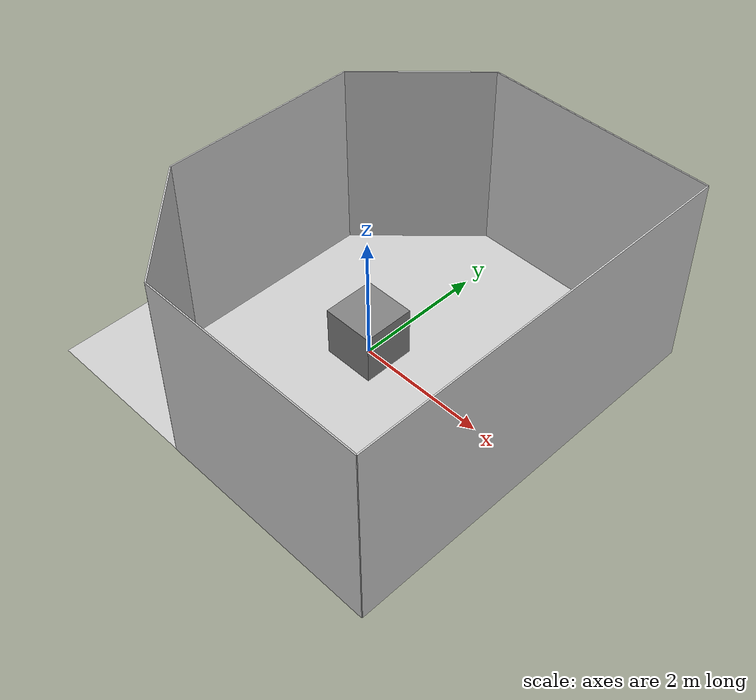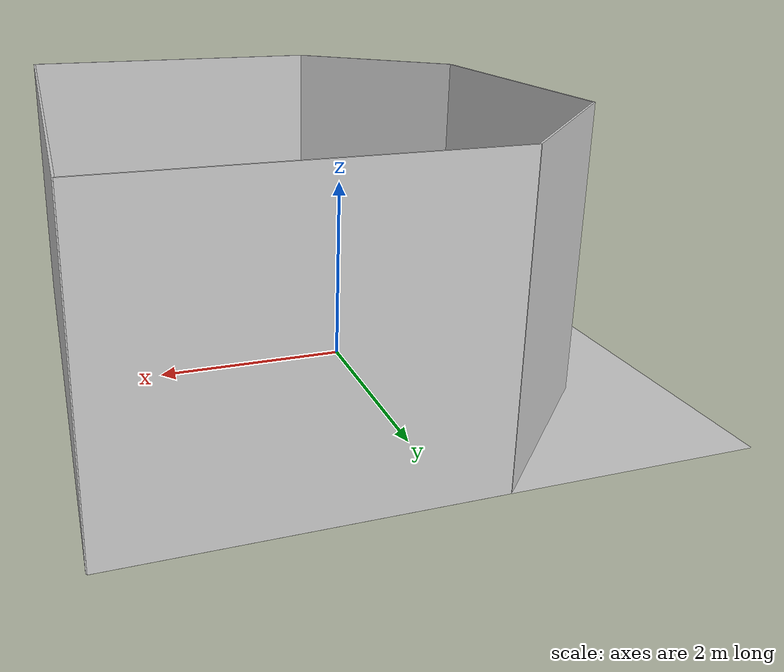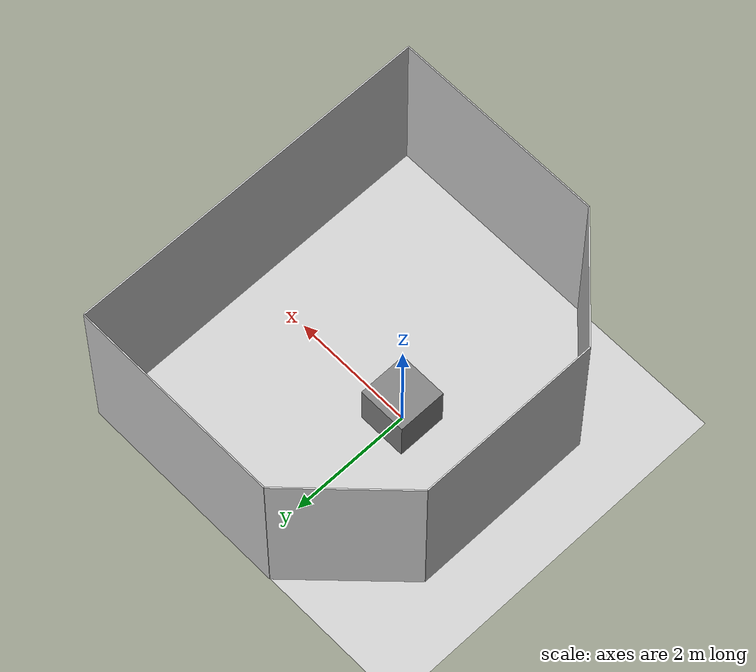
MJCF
<mujoco model="table_arena">
  <asset>
    <texture builtin="gradient" height="256" rgb1=".9 .9 1." rgb2=".2 .3 .4" type="skybox" width="256"/>
    <texture file="../textures/light-gray-floor-tile.png" type="2d" name="texplane"/>
    <material name="floorplane" reflectance="0.01" shininess="0.0" specular="0.0" texrepeat="2 2" texture="texplane" texuniform="true"/>
    <!-- ceramic table texture and material-->
    <texture file="../textures/ceramic.png" type="cube" name="tex-ceramic"/>
    <material name="table_ceramic" reflectance="0.0" shininess="0.0" specular="0.2" texrepeat="1 1" texture="tex-ceramic" />
    <!-- steel legs -->
    <texture file="../textures/steel-brushed.png" type="cube" name="tex-steel-brushed"/>
    <material name="table_legs_metal" reflectance="0.8" shininess="0.8" texrepeat="1 1" texture="tex-steel-brushed" />
    <!-- plaster walls -->
    <texture file="../textures/light-gray-plaster.png" type="2d" name="tex-light-gray-plaster"/>
    <material name="walls_mat" reflectance="0.0" shininess="0.1" specular="0.1" texrepeat="3 3" texture="tex-light-gray-plaster" texuniform="true" />
    <!-- added table texture and material for domain randomization -->
    <texture  name="textable" builtin="flat" height="512" width="512" rgb1="0.5 0.5 0.5" rgb2="0.5 0.5 0.5"/>
    <material name="table_mat" texture="textable" />

  </asset>
  <worldbody>
    <!-- Floor -->
    <geom condim="3" group="1" material="floorplane" name="floor" pos="0 0 0" size="3 3 .125" type="plane"/>
    <!-- Walls (visual only) -->
    <geom pos="-1.25 2.25 1.5" quat="0.6532815 0.6532815 0.2705981 0.2705981" size="1.06 1.5 0.01" type="box" conaffinity="0" contype="0" group="1" name="wall_leftcorner_visual" material="walls_mat"/>
    <geom pos="-1.25 -2.25 1.5" quat="0.6532815 0.6532815 -0.2705981 -0.2705981" size="1.06 1.5 0.01" type="box" conaffinity="0" contype="0" group="1" name="wall_rightcorner_visual" material="walls_mat"/>
    <geom pos="1.25 3 1.5" quat="0.7071 0.7071 0 0" size="1.75 1.5 0.01" type="box" conaffinity="0" contype="0" group="1" name="wall_left_visual" material="walls_mat"/>
    <geom pos="1.25 -3 1.5" quat="0.7071 -0.7071 0 0" size="1.75 1.5 0.01" type="box" conaffinity="0" contype="0" group="1" name="wall_right_visual" material="walls_mat"/>
    <geom pos="-2 0 1.5" quat="0.5 0.5 0.5 0.5" size="1.5 1.5 0.01" type="box" conaffinity="0" contype="0" group="1" name="wall_rear_visual" material="walls_mat"/>
    <geom pos="3 0 1.5" quat="0.5 0.5 -0.5 -0.5" size="3 1.5 0.01" type="box" conaffinity="0" contype="0" group="1" name="wall_front_visual" material="walls_mat"/>
    <!-- Table body -->
    <body name="table" pos="0 0 0.4">
      <geom pos="0 0 0" size="0.4 0.4 0.4" type="box" group="0" name="table_collision" friction="1 0.005 0.0001"/>
      <geom pos="0 0 0" size="0.4 0.4 0.4" type="box" conaffinity="0" contype="0" group="1" name="table_visual" material="table_ceramic"/>
      <site pos="0 0 0.4" name="table_top" size="0.001 0.001 0.001" rgba="0 0 0 0"/>
      <!-- Legs (visual only) -->
      <geom pos="0 0 0" size="0.05 0.1" type="cylinder" conaffinity="0" contype="0" group="1" name="table_leg1_visual" material="table_legs_metal"/>
      <geom pos="0 0 0" size="0.05 0.1" type="cylinder" conaffinity="0" contype="0" group="1" name="table_leg2_visual" material="table_legs_metal"/>
      <geom pos="0 0 0" size="0.05 0.1" type="cylinder" conaffinity="0" contype="0" group="1" name="table_leg3_visual" material="table_legs_metal"/>
      <geom pos="0 0 0" size="0.05 0.1" type="cylinder" conaffinity="0" contype="0" group="1" name="table_leg4_visual" material="table_legs_metal"/>
    </body>
    <light pos="1.0 1.0 1.5" dir="-0.2 -0.2 -1" specular="0.3 0.3 0.3" directional="true" castshadow="false"/>
    <!-- front view -->
    <camera mode="fixed" name="frontview" pos="1.6 0 1.45" quat="0.56 0.43 0.43 0.56"/>
    <!-- bird view -->
    <camera mode="fixed" name="birdview" pos="-0.2 0 3.0" quat="0.7071 0 0 0.7071"/>
    <!-- agent view -->
    <camera mode="fixed" name="agentview" pos="0.5 0 1.35" quat="0.653 0.271 0.271 0.653"/>
    <!-- side view -->
    <camera mode="fixed" name="sideview" pos="-0.05651774593317116 1.2761224129427358 1.4879572214102434" quat="0.009905065491771751 0.006877963156909582 0.5912228352893879 0.806418094001364" />

<camera name="teacher_0" pos="0.5 0 1.35" quat="0.653 0.271 0.271 0.653"/>
<camera name="teacher_1" pos="0.7742607383199331 0.3390494981902051 2.1163069016111886" quat="0.4209729731082916 0.13771885633468628 0.27876538038253784 0.8521180152893066" />
<camera name="teacher_2" pos="1.1989083078822722 -0.8360239233139897 1.3147423950446668" quat="0.7538022398948669 0.4946337044239044 0.23731762170791626 0.3616626262664795" />
<camera name="teacher_3" pos="1.2767419038903016 -0.31758190633268474 1.6877672654386051" quat="0.6451565623283386 0.4080793261528015 0.3453000783920288 0.5459049344062805" />

<camera name="agentview_0" pos="0.4891050110201337 -0.5291666812710062 2.220076390708039" quat="0.8818037509918213 0.2637408375740051 0.11203432083129883 0.37458112835884094" />

<camera name="agentview_1" pos="0.7742607383199331 0.3390494981902051 2.1163069016111886" quat="0.4209729731082916 0.13771885633468628 0.27876538038253784 0.8521180152893066" />

<camera name="agentview_2" pos="1.1989083078822722 -0.8360239233139897 1.3147423950446668" quat="0.7538022398948669 0.4946337044239044 0.23731762170791626 0.3616626262664795" />

<camera name="agentview_3" pos="1.2767419038903016 -0.31758190633268474 1.6877672654386051" quat="0.6451565623283386 0.4080793261528015 0.3453000783920288 0.5459049344062805" />

<camera name="agentview_4" pos="0.859477789566143 -0.6217700491995442 1.4052548736662072" quat="0.7069156169891357 0.4511702060699463 0.2930522561073303 0.4591687023639679" />

<camera name="agentview_5" pos="0.7998772814266073 -0.7807872486324687 2.225978657915639" quat="0.8404864072799683 0.30201226472854614 0.15212422609329224 0.4233551025390625" />

<camera name="agentview_6" pos="1.0094099444914602 0.19825958464095947 1.4820376697513593" quat="0.375403493642807 0.25273430347442627 0.4980055093765259 0.7397215366363525" />

<camera name="agentview_7" pos="0.49832686639814633 -0.04811989245529134 1.6196037833028794" quat="0.6375752091407776 0.30266356468200684 0.3038116693496704 0.6399933695793152" />

<camera name="agentview_8" pos="0.3381595751099744 0.18479687865346558 1.6446002596052993" quat="0.4476514458656311 0.1776116043329239 0.32320940494537354 0.8146151304244995" />

<camera name="agentview_9" pos="0.7171574315908165 -0.09730914604152949 1.8707466434908882" quat="0.534292995929718 0.1548784077167511 0.23135912418365479 0.798133134841919" />

<camera name="agentview_10" pos="0.9586501206089006 -0.5619728451925469 1.6878811926966062" quat="0.7316178679466248 0.43495044112205505 0.268250048160553 0.45121562480926514" />

<camera name="agentview_11" pos="1.1038584893081564 0.16319928520211013 1.6867506294205843" quat="0.6574869155883789 0.29458731412887573 0.283557653427124 0.6328697204589844" />

<camera name="agentview_12" pos="0.9549068448529965 -0.9037195254014406 2.3588142488676405" quat="0.7831080555915833 0.3992983102798462 0.21656835079193115 0.4247361719608307" />

<camera name="agentview_13" pos="0.9879820515372502 0.6289295715086562 1.6258804701047471" quat="0.4222685992717743 0.28495997190475464 0.4813523292541504 0.7132930755615234" />

<camera name="agentview_14" pos="0.586497364158499 0.3568241094416729 1.4569297571644633" quat="0.4750167727470398 0.20420485734939575 0.33805274963378906 0.7863712310791016" />

<camera name="agentview_15" pos="1.1855149761636736 0.4078203805493725 1.9764650811390894" quat="0.5090322494506836 0.22953912615776062 0.3410152792930603 0.7562448978424072" />

<camera name="agentview_16" pos="0.9290665425871012 0.33636851923666894 1.5231409054961147" quat="0.5958797335624695 0.2724504768848419 0.3141297698020935 0.6870374083518982" />

<camera name="agentview_17" pos="0.2050395506918102 -0.05965447638197082 1.8567140278713168" quat="0.6822014451026917 0.19015604257583618 0.18956446647644043 0.6800788044929504" />

<camera name="agentview_18" pos="0.6255821133999817 0.2817457928698024 2.3193002735374124" quat="0.5801279544830322 0.1701011210680008 0.22412735223770142 0.7643846273422241" />

<camera name="agentview_19" pos="0.5050919731986072 -0.03595329289570307 1.5139300284383483" quat="0.7613260746002197 0.347389817237854 0.22725898027420044 0.4980524182319641" />

<camera name="agentview_20" pos="1.204146734290207 -1.117548322422795 1.4424498016244365" quat="0.6856412887573242 0.43769651651382446 0.3129756450653076 0.49026909470558167" />

<camera name="agentview_21" pos="0.9425344236052016 0.4647643502603812 2.1770631235299067" quat="0.49025559425354004 0.18938438594341278 0.306565523147583 0.7935998439788818" />

<camera name="agentview_22" pos="0.7635054229824481 -0.4975290847825446 1.677526337398571" quat="0.8054598569869995 0.324951708316803 0.18542981147766113 0.45962634682655334" />

<camera name="agentview_23" pos="1.1947084911140735 -0.23325543910780283 1.640401169976665" quat="0.5142547488212585 0.3527064919471741 0.44216829538345337 0.6446918249130249" />

<camera name="agentview_24" pos="0.41288305939416936 -0.2049882657336012 1.6663186640779666" quat="0.8203903436660767 0.2516230344772339 0.15056252479553223 0.49089348316192627" />

<camera name="agentview_25" pos="0.6544077068693399 -0.09232505865204552 1.7191911232966701" quat="0.7698500156402588 0.22049623727798462 0.16491037607192993 0.5757750868797302" />

<camera name="agentview_26" pos="0.8592548563007787 -0.8074958309326334 2.1893687739498153" quat="0.8415790796279907 0.3686857521533966 0.15839552879333496 0.3615609407424927" />

<camera name="agentview_27" pos="0.9530445442185886 -0.01345837648545249 1.645448408752171" quat="0.7327343821525574 0.2621215879917145 0.21152961254119873 0.5913101434707642" />

<camera name="agentview_28" pos="0.357785377794562 0.14342388132567854 1.7390236904007783" quat="0.5167106986045837 0.1833292841911316 0.2796408534049988 0.7881633639335632" />

<camera name="agentview_29" pos="0.34974649000954494 -0.42206204871974046 1.8438624870912996" quat="0.869763970375061 0.2515091598033905 0.11793887615203857 0.40785321593284607" />

<camera name="agentview_30" pos="0.726006835204871 -0.15243088011963035 2.1449638853696484" quat="0.7305971384048462 0.20309728384017944 0.17460089921951294 0.62808758020401" />

<camera name="agentview_31" pos="0.9548252355332458 -0.33432936562777715 2.289696832308087" quat="0.8334416747093201 0.33006420731544495 0.16319024562835693 0.41207000613212585" />

<camera name="agentview_32" pos="1.203335897275445 -0.6724019233981124 1.5722539349002744" quat="0.6325731873512268 0.45350053906440735 0.365814745426178 0.5102627873420715" />

<camera name="agentview_33" pos="1.2255146092791878 -0.4906534857120183 1.6798409703097255" quat="0.6862019300460815 0.37592002749443054 0.2992008924484253 0.5461592078208923" />

<camera name="agentview_34" pos="1.3788134863617236 0.36362244168012003 2.0472919501478906" quat="0.5259304642677307 0.26583462953567505 0.36445480585098267 0.7210420966148376" />

<camera name="agentview_35" pos="0.7439112497969824 -0.34705991838127515 2.492816831655849" quat="0.7298306226730347 0.20125317573547363 0.1736764907836914 0.6298258900642395" />

<camera name="agentview_36" pos="0.704560750005031 0.15994978301480048 1.1287041061308436" quat="0.5190490484237671 0.3849343955516815 0.4545999765396118 0.6129865050315857" />

<camera name="agentview_37" pos="1.2339463271918494 -0.6499952882001393 2.0601466720823614" quat="0.7089244723320007 0.38748475909233093 0.2826393246650696 0.5171042084693909" />

<camera name="agentview_38" pos="0.9561193081864889 0.704175666306084 1.6931930125572827" quat="0.41315847635269165 0.19548247754573822 0.38039660453796387 0.8039806485176086" />

<camera name="agentview_39" pos="0.926949761958404 -0.5118745626837203 1.3118930859696378" quat="0.7294354438781738 0.5432002544403076 0.2483210563659668 0.33345744013786316" />

<camera name="agentview_40" pos="0.7575224545928441 -0.18207480209876623 1.1240786857157918" quat="0.6484071612358093 0.4665485918521881 0.3513561487197876 0.48831304907798767" />

<camera name="agentview_41" pos="0.6658036014335682 -0.16081957949413497 1.4992908948831838" quat="0.5908198356628418 0.36892321705818176 0.38003087043762207 0.6086083650588989" />

<camera name="agentview_42" pos="0.684135071561278 0.8233247655649845 2.455397297547042" quat="0.4276808500289917 0.15699616074562073 0.3067622184753418 0.8356662392616272" />

<camera name="agentview_43" pos="1.517280287748152 -0.1275671724029747 1.7635796550097915" quat="0.5842841267585754 0.34601759910583496 0.37405943870544434 0.6316354870796204" />

<camera name="agentview_44" pos="0.4845264338929839 -0.34359643247464294 1.3491740818562736" quat="0.7754257917404175 0.4536336362361908 0.2217949628829956 0.3791286051273346" />

<camera name="agentview_45" pos="1.1161503941832005 -0.632166513630742 1.2267363275922245" quat="0.6109238862991333 0.46735715866088867 0.3882683515548706 0.5075401067733765" />

<camera name="agentview_46" pos="1.1962256925368768 0.3497462495716146 1.645590196814622" quat="0.6207641363143921 0.35407036542892456 0.3465629816055298 0.6076020002365112" />

<camera name="agentview_47" pos="0.7249430952158644 -0.29341944129808467 2.4039361054835826" quat="0.7773288488388062 0.2689610421657562 0.18595731258392334 0.5374380350112915" />

<camera name="agentview_48" pos="0.4617067435730643 0.2752317995014256 1.3566752573308374" quat="0.4696378707885742 0.21740508079528809 0.3594609498977661 0.776506781578064" />

<camera name="agentview_49" pos="1.3650450394327351 0.6958164517394887 2.171532110113484" quat="0.4486442506313324 0.2085484266281128 0.3663214445114136 0.788057267665863" />

<camera name="agentview_50" pos="0.3596307264176725 0.4434040076269891 1.010742888705906" quat="0.445324182510376 0.324618399143219 0.49153923988342285 0.6743128895759583" />

<camera name="agentview_51" pos="0.3868860099139924 0.42025375396251796 1.4606447468123807" quat="0.4221457839012146 0.24435076117515564 0.4373258948326111 0.7555340528488159" />

<camera name="agentview_52" pos="0.6179452724583816 -0.5325314833345877 1.9893176948518634" quat="0.8530057668685913 0.32785266637802124 0.1456834077835083 0.37903836369514465" />

<camera name="agentview_53" pos="1.2237672546106222 0.21394509656844432 1.8846736683419707" quat="0.5429676175117493 0.2711159884929657 0.3550529479980469 0.7110694050788879" />

<camera name="agentview_54" pos="0.6339509069876654 0.869949166303602 1.1790517461008454" quat="0.3545255959033966 0.27124276757240295 0.5437412261962891 0.7106927037239075" />

<camera name="agentview_55" pos="0.6397987226262098 0.03736224960581658 1.5286838086044332" quat="0.6823354959487915 0.26731181144714355 0.24819254875183105 0.6335321664810181" />

<camera name="agentview_56" pos="2.3019321686015823 1.657006507511082 1.3107386199165367" quat="0.3613547384738922 0.26357677578926086 0.5270715355873108 0.7225967049598694" />

<camera name="agentview_57" pos="0.9294563633785848 -0.14932214347511716 2.146019200071275" quat="0.794012188911438 0.25654351711273193 0.16944003105163574 0.5244237780570984" />

<camera name="agentview_58" pos="1.614531996419387 0.41552270558428117 2.9476719542713856" quat="0.5964765548706055 0.21997930109500885 0.26708924770355225 0.724215567111969" />

<camera name="agentview_59" pos="0.7474328290160188 0.47557158416838263 1.4929801560366402" quat="0.5169467329978943 0.2558290660381317 0.36232733726501465 0.7321451306343079" />

<camera name="agentview_60" pos="0.36143508406921565 0.1912609797011027 1.5673562867152173" quat="0.3936860263347626 0.1064869686961174 0.2384026050567627 0.8813828825950623" />

<camera name="agentview_61" pos="0.746450195228852 -0.9459304079073708 2.1137475049348793" quat="0.8390040993690491 0.36469048261642456 0.1609797477722168 0.37034887075424194" />

<camera name="agentview_62" pos="0.6469710275207987 -0.3809345243423767 1.3561084603542353" quat="0.7756574153900146 0.389874130487442 0.22290515899658203 0.4434715807437897" />

<camera name="agentview_63" pos="0.7622186537029589 0.9554746702587923 1.6220830220660454" quat="0.37892037630081177 0.24404288828372955 0.4833509922027588 0.7504892945289612" />

<camera name="agentview_64" pos="1.0425445618010423 0.19396290675737946 1.929127825494025" quat="0.4696350693702698 0.20633430778980255 0.3452872037887573 0.7859044671058655" />

<camera name="agentview_65" pos="1.2968236144719985 0.7447664823420673 2.293149568902449" quat="0.5053515434265137 0.23315148055553436 0.3480534553527832 0.7543997764587402" />

<camera name="agentview_66" pos="1.1533044302504458 0.19984078283582335 1.2094284245674465" quat="0.572364091873169 0.38439297676086426 0.403827428817749 0.6013023257255554" />

<camera name="agentview_67" pos="1.074337659520389 0.9574067893179484 2.3046917328103462" quat="0.3616120517253876 0.16640068590641022 0.38348162174224854 0.8333603739738464" />

<camera name="agentview_68" pos="0.4574975325368374 -0.2134519909409012 1.0939098761752553" quat="0.7238669991493225 0.5449944138526917 0.25447404384613037 0.33799511194229126" />

<camera name="agentview_69" pos="0.24206509456239458 0.5446169993698028 1.6488127224778193" quat="0.5525028109550476 0.1605890542268753 0.22828000783920288 0.7853918075561523" />

<camera name="agentview_70" pos="1.8787902959753222 -1.2092719835723376 2.742592074569111" quat="0.7985838055610657 0.38795092701911926 0.20107918977737427 0.41391459107398987" />

<camera name="agentview_71" pos="0.9650912985999405 0.37415831886602263 1.6093519747262666" quat="0.46143046021461487 0.28122764825820923 0.43790102005004883 0.7184954881668091" />

<camera name="agentview_72" pos="1.1518824877241103 -0.8513812755579535 1.732028128776692" quat="0.7514092326164246 0.49560070037841797 0.23984628915786743 0.36364513635635376" />

<camera name="agentview_73" pos="0.8456448474842537 0.34933085045543855 1.6567705176383098" quat="0.4579049348831177 0.2007298767566681 0.34770292043685913 0.7931792736053467" />

<camera name="agentview_74" pos="0.6575058033281131 -0.15536778832679862 2.1155823480208396" quat="0.655337393283844 0.23831002414226532 0.24495244026184082 0.6736022233963013" />

<camera name="agentview_75" pos="1.337166525032584 0.1967592145503006 1.4407829015376343" quat="0.6247392892837524 0.35326194763183594 0.34275442361831665 0.6061569452285767" />

<camera name="agentview_76" pos="1.5644104160366485 -0.287139232878163 1.586515016770194" quat="0.6287966370582581 0.40260589122772217 0.35870277881622314 0.5602279901504517" />

<camera name="agentview_77" pos="0.9209037649936174 -0.5465175959666141 1.082034830323205" quat="0.7100383043289185 0.5349520444869995 0.27553772926330566 0.36571943759918213" />

<camera name="agentview_78" pos="1.0177262581603874 1.203636346417688 1.3850726510405553" quat="0.38225626945495605 0.27197855710983276 0.5119811296463013 0.7195717096328735" />

<camera name="agentview_79" pos="0.9768166083064387 0.9710863500752632 2.445910536354314" quat="0.3606789708137512 0.1458226442337036 0.3452962040901184 0.8540589213371277" />

<camera name="agentview_80" pos="0.46800633985331 0.20669066043403816 1.4105978748924963" quat="0.4962416887283325 0.2207271158695221 0.3412429690361023 0.7671875357627869" />

<camera name="agentview_81" pos="0.7597383475950947 1.0208385341336854 1.6826196683695163" quat="0.3408737778663635 0.19665634632110596 0.45939743518829346 0.7962948083877563" />

<camera name="agentview_82" pos="1.167891550147588 -0.40787448029426054 1.9914379931623385" quat="0.6911005973815918 0.3622710108757019 0.2903628349304199 0.5539218187332153" />

<camera name="agentview_83" pos="1.3083783883523414 0.3974713400051925 1.7257596044106718" quat="0.55921870470047 0.32519158720970154 0.3833439350128174 0.6592208743095398" />

<camera name="agentview_84" pos="0.3886271352000387 0.42032772583653877 1.874223926150578" quat="0.4462549090385437 0.12295632809400558 0.23546016216278076 0.8545740842819214" />

<camera name="agentview_85" pos="1.074240947303795 1.174577921579807 2.4942363743286857" quat="0.4287331998348236 0.1950497329235077 0.3652909994125366 0.8029358983039856" />

<camera name="agentview_86" pos="0.833939361825283 -0.04257007595709918 1.6140791630808924" quat="0.6588687896728516 0.24818800389766693 0.25032925605773926 0.6645526885986328" />

<camera name="agentview_87" pos="1.9444485264071725 -0.24269689719929144 1.763084180137706" quat="0.6295068860054016 0.47377660870552063 0.3703261613845825 0.49205219745635986" />

<camera name="agentview_88" pos="1.7039154087504804 -0.4392964934733166 2.2560311249592893" quat="0.7184972167015076 0.39451128244400024 0.2756972312927246 0.5021092295646667" />

<camera name="agentview_89" pos="0.6037170821848776 0.4128464628528646 1.3558631005235273" quat="0.35763975977897644 0.1878873109817505 0.42543745040893555 0.8098117709159851" />

<camera name="agentview_90" pos="1.2057629809539954 0.29632496623005555 1.4844029314462601" quat="0.5124240517616272 0.25835180282592773 0.3686854839324951 0.7312638759613037" />

<camera name="agentview_91" pos="0.5024926016799618 -0.14469462316758122 1.8207923585575254" quat="0.6646802425384521 0.2281596064567566 0.23098021745681763 0.6728978157043457" />

<camera name="agentview_92" pos="1.2952144250553248 0.005805216532752211 1.8379441247411732" quat="0.8073952198028564 0.29106542468070984 0.17405056953430176 0.4828045666217804" />

<camera name="agentview_93" pos="0.866567823633333 0.24366704161110497 1.7305140882973005" quat="0.4743328094482422 0.21364107728004456 0.3507245182991028 0.778689980506897" />

<camera name="agentview_94" pos="0.9649059559395754 -0.2105481159856992 1.4230514069930078" quat="0.6127142310142517 0.45820626616477966 0.3856331706047058 0.5156694054603577" />

<camera name="agentview_95" pos="0.8576774093815915 0.06362209992608281 2.2655173747333675" quat="0.5690973401069641 0.18531900644302368 0.24805212020874023 0.7617449164390564" />

<camera name="agentview_96" pos="0.7163888297737615 0.2216976775274962 2.1154902782102445" quat="0.5488844513893127 0.17783652245998383 0.2517440915107727 0.7769972085952759" />

<camera name="agentview_97" pos="1.1424281907721474 -0.2845198511748114 1.7393082326630855" quat="0.7634779810905457 0.37570616602897644 0.23193985223770142 0.4713283181190491" />

<camera name="agentview_98" pos="0.6697257709094091 0.4305528574789982 1.979127714044023" quat="0.4145764112472534 0.15368181467056274 0.3117625117301941 0.8410186171531677" />

<camera name="agentview_99" pos="1.1081830488996431 0.25131310645626936 2.512057018886358" quat="0.5493846535682678 0.15811321139335632 0.22692173719406128 0.7884689569473267" />

<camera name="agentview_100" pos="0.43837112373190995 -0.2911484280300361 1.4328789111360758" quat="0.8187793493270874 0.417106568813324 0.17906701564788818 0.35150769352912903" />

<camera name="agentview_101" pos="1.0425732977815245 0.2193093222000872 1.7020422445596042" quat="0.5648834705352783 0.38579511642456055 0.4113863706588745 0.6023539900779724" />

<camera name="agentview_102" pos="1.3343763609113266 -0.10386176968555408 1.23391002610499" quat="0.6173591017723083 0.3630625009536743 0.35378026962280273 0.6015752553939819" />

<camera name="agentview_103" pos="0.8576018252423123 -0.36593011276655585 1.8659267317150117" quat="0.7639420032501221 0.42784568667411804 0.23603790998458862 0.42145827412605286" />

<camera name="agentview_104" pos="1.2361377217970457 -0.36507742542369026 1.97648473038866" quat="0.7121475338935852 0.38954445719718933 0.28027814626693726 0.5123916268348694" />

<camera name="agentview_105" pos="1.6702618420698632 -0.31151383726556203 1.7423990817755395" quat="0.6222571134567261 0.38683781027793884 0.3593066930770874 0.5779715180397034" />

<camera name="agentview_106" pos="1.2687124919357406 -0.6979022580498119 1.8933053183796105" quat="0.7147062420845032 0.42453813552856445 0.28386908769607544 0.47789159417152405" />

<camera name="agentview_107" pos="1.0994850228937318 -0.05464032542504127 1.592140459012389" quat="0.5280342698097229 0.3038580119609833 0.3955209255218506 0.687323272228241" />

<camera name="agentview_108" pos="1.8466870428217619 -0.49330792301925747 1.5887095940429679" quat="0.6726085543632507 0.47055190801620483 0.32738804817199707 0.46796974539756775" />

<camera name="agentview_109" pos="0.4652163295631557 0.45133858225093043 2.0323750433784737" quat="0.5564476251602173 0.1563469022512436 0.22073763608932495 0.7856183648109436" />

<camera name="agentview_110" pos="0.46404913667642717 -0.524286267502702 1.4089543187784535" quat="0.8036442995071411 0.3784269094467163 0.19566726684570312 0.41552767157554626" />

<camera name="agentview_111" pos="0.8601488484475857 0.5958053745112363 2.0069490421773564" quat="0.40712761878967285 0.13147275149822235 0.27775752544403076 0.8601236343383789" />

<camera name="agentview_112" pos="1.5399447751544784 0.9689820681409964 1.6811223117153602" quat="0.4166888892650604 0.3030913174152374 0.504131555557251 0.6930782198905945" />

<camera name="agentview_113" pos="0.7412271016427248 0.6204998535273191 3.1812467808881957" quat="0.37655192613601685 0.10563067346811295 0.24858272075653076 0.8861473798751831" />

<camera name="agentview_114" pos="1.1048687724856394 0.970723002690557 1.8912084800706006" quat="0.437811940908432 0.2109261453151703 0.3793301582336426 0.787362277507782" />

<camera name="agentview_115" pos="0.8098134636116538 0.49908147438278977 1.68234522648775" quat="0.4598902761936188 0.18283845484256744 0.32102686166763306 0.8074731826782227" />

<camera name="agentview_116" pos="1.351252567804051 -0.553715562546626 1.416327574762628" quat="0.6849491596221924 0.4934219419956207 0.31334108114242554 0.4349678158760071" />

<camera name="agentview_117" pos="1.0846655333568407 0.3443128002099152 2.100991409046649" quat="0.5587190985679626 0.2168375849723816 0.28962868452072144 0.7462773323059082" />

<camera name="agentview_118" pos="1.330162028397521 0.30502386270077014 1.486576028112281" quat="0.49499180912971497 0.3218541145324707 0.43995964527130127 0.676630437374115" />

<camera name="agentview_119" pos="1.7180480866684769 -0.08764002546503268 1.1873496685334715" quat="0.577305257320404 0.4424821734428406 0.4174611568450928 0.544660210609436" />

<camera name="agentview_120" pos="0.7717485708600802 -0.1190291828992289 1.8103715255401305" quat="0.6698596477508545 0.2807164490222931 0.2656717300415039 0.6339595317840576" />

<camera name="agentview_121" pos="0.8470706498095004 0.729261253128433 1.9397404430518028" quat="0.4255937337875366 0.2063273787498474 0.3843594789505005 0.7928220629692078" />

<camera name="agentview_122" pos="1.0024066900482393 1.2014970361096413 1.8112056185785468" quat="0.3512209355831146 0.2176850587129593 0.47973543405532837 0.77402263879776" />

<camera name="agentview_123" pos="0.7442860174232173 -0.21528626957799957 1.8946409206228696" quat="0.8235408067703247 0.3129730820655823 0.16806817054748535 0.44224584102630615" />

<camera name="agentview_124" pos="0.4011679866751207 0.3046833455211627 1.1975094395309158" quat="0.46380874514579773 0.2761740982532501 0.43067383766174316 0.7232767939567566" />

<camera name="agentview_125" pos="0.669807130123113 -0.28798280291787 1.828306011649256" quat="0.720392107963562 0.2760685086250305 0.22768008708953857 0.5941241383552551" />

<camera name="agentview_126" pos="1.1041337449044062 0.8885728823036504 1.9146719075095966" quat="0.44687750935554504 0.2795315980911255 0.4506641626358032 0.7204611897468567" />

<camera name="agentview_127" pos="0.6211140649670601 0.1715873958089525 1.3738479260204834" quat="0.7042157649993896 0.3217834234237671 0.26302826404571533 0.5756315588951111" />

<camera name="agentview_128" pos="0.9587559527163536 0.7641938717274795 2.4734357579960418" quat="0.45638757944107056 0.16547496616840363 0.29800164699554443 0.8219022154808044" />

<camera name="agentview_129" pos="0.6820654147892058 0.10711937061384404 1.8208715537007991" quat="0.6481158137321472 0.17445506155490875 0.192676842212677 0.7158118486404419" />

<camera name="agentview_130" pos="1.2050557609330594 -0.1681288604692095 1.4426118075653322" quat="0.6540231108665466 0.4081587493419647 0.3372042179107666 0.5403273701667786" />

<camera name="agentview_131" pos="0.5562169569838826 0.41655189575936225 1.5895724835578242" quat="0.4000948369503021 0.16977155208587646 0.3517942428588867 0.8290613889694214" />

<camera name="agentview_132" pos="1.531522114822832 0.7633764963546122 1.791143633625525" quat="0.5021461248397827 0.313864529132843 0.4271041750907898 0.6833156943321228" />

<camera name="agentview_133" pos="0.9455313483884049 0.12452323393334068 1.5691233012117767" quat="0.5836259722709656 0.25943630933761597 0.312555730342865 0.7031232714653015" />

<camera name="agentview_134" pos="1.0478301389858222 0.13829961395394677 1.2720064471905392" quat="0.5518786907196045 0.3033497631549835 0.3741777539253235 0.6807346940040588" />

<camera name="agentview_135" pos="0.35758146349261993 -0.09353480157402523 1.610212812060591" quat="0.7900431156158447 0.2141602635383606 0.15028858184814453 0.5544189214706421" />

<camera name="agentview_136" pos="1.4177757961545183 0.45285757494980133 1.9508837812128779" quat="0.39231106638908386 0.22158798575401306 0.43905109167099 0.7773191332817078" />

<camera name="agentview_137" pos="0.6953678011542166 -0.4476504650867224 2.1433615279329112" quat="0.850763201713562 0.2521682679653168 0.13103598356246948 0.44208866357803345" />

<camera name="agentview_138" pos="0.6064605870178315 1.0776431610215496 2.0139261262618935" quat="0.3713185489177704 0.17965316772460938 0.396747887134552 0.8200235962867737" />

<camera name="agentview_139" pos="1.4850469477565538 0.9898111704420185 1.005575567409103" quat="0.3945879638195038 0.30276235938072205 0.5281109809875488 0.688283383846283" />

<camera name="agentview_140" pos="0.5948711305955909 -0.4966400818007949 1.9924454872145418" quat="0.735055685043335 0.20822949707508087 0.17586559057235718 0.6208099722862244" />

<camera name="agentview_141" pos="0.16600607118628247 -0.43724791663571483 1.8660733230536963" quat="0.8508622050285339 0.31874942779541016 0.14651626348495483 0.3911074697971344" />

<camera name="agentview_142" pos="1.2546427867094152 0.7815840971120442 1.567856630849549" quat="0.38136088848114014 0.2854764461517334 0.526902437210083 0.7038756608963013" />

<camera name="agentview_143" pos="1.7846671499533515 1.0611704571916438 1.50340129673419" quat="0.45019254088401794 0.338565468788147 0.49661827087402344 0.660356342792511" />

<camera name="agentview_144" pos="0.2626800068912134 -0.16393310670161382 1.777581861386121" quat="0.8324331641197205 0.26308393478393555 0.1469658613204956 0.465019553899765" />

<camera name="agentview_145" pos="1.176016631136012 -0.1937439684240958 1.688655470872851" quat="0.7248284816741943 0.3180295526981354 0.24554681777954102 0.5596316456794739" />

<camera name="agentview_146" pos="0.6953688622223291 -0.7266862348904727 1.7331265014037478" quat="0.8128494620323181 0.37103283405303955 0.18644952774047852 0.40846899151802063" />

<camera name="agentview_147" pos="1.3340916006056556 0.5094721566167437 2.120192318850815" quat="0.6002300381660461 0.23667025566101074 0.28024959564208984 0.710753858089447" />

<camera name="agentview_148" pos="0.7010746755608179 0.27290497539739 1.6345707790906834" quat="0.611307680606842 0.3095638155937195 0.32904255390167236 0.6497726440429688" />

<camera name="agentview_149" pos="0.4528136945236591 0.04133021362842137 1.6244143363109276" quat="0.5291310548782349 0.201371431350708 0.2931894063949585 0.7703956961631775" />

<camera name="agentview_150" pos="0.18477226897313107 -0.13465747108126278 1.386893236271835" quat="0.8169780969619751 0.2344684600830078 0.14533650875091553 0.5064077973365784" />

<camera name="agentview_151" pos="0.6462610214173365 0.5833438178586289 2.2038497706614706" quat="0.44089475274086 0.11823862046003342 0.23046493530273438 0.8593704104423523" />

<camera name="agentview_152" pos="0.935301950299533 0.6696421220227187 2.960966168422389" quat="0.5013117790222168 0.2033020257949829 0.3160744309425354 0.7793917655944824" />

<camera name="agentview_153" pos="1.195401745857386 0.05222957395843571 1.7609929667083761" quat="0.5650338530540466 0.31063908338546753 0.3682393431663513 0.6698055267333984" />

<camera name="agentview_154" pos="1.4178002297880925 -0.03323016174214902 2.040747238323328" quat="0.6743619441986084 0.32603737711906433 0.2883775234222412 0.5964679718017578" />

<camera name="agentview_155" pos="0.39125376081807256 0.42375361850631377 1.2275529226928927" quat="0.4787992238998413 0.2993135154247284 0.4374893307685852 0.6998327970504761" />

<camera name="agentview_156" pos="1.325997729919727 0.43204128940460146 1.4577969415176688" quat="0.6084270477294922 0.3667494058609009 0.3633263111114502 0.6027483344078064" />

<camera name="agentview_157" pos="1.0316535866661887 0.013626691468670816 1.4399049407886155" quat="0.6312663555145264 0.4377606511116028 0.3648245334625244 0.5260904431343079" />

<camera name="agentview_158" pos="0.5549967156317639 -0.43981181608963177 2.027170253262173" quat="0.7759077548980713 0.2870784103870392 0.19492477178573608 0.5268374085426331" />

<camera name="agentview_159" pos="1.4693489164106488 0.3882576405433039 1.4315806013784877" quat="0.5354812741279602 0.39040911197662354 0.44119298458099365 0.6051356792449951" />

<camera name="agentview_160" pos="0.9512464618527883 0.514550083079175 1.3082004313629847" quat="0.4599880874156952 0.3468785583972931 0.49213141202926636 0.6526046991348267" />

<camera name="agentview_161" pos="1.2372691468820343 0.056123472186824154 1.4424963109247368" quat="0.5651707649230957 0.3797086775302887 0.4084382653236389 0.6079323887825012" />

<camera name="agentview_162" pos="0.4305620990437824 -0.39622996473055827 2.007005527515683" quat="0.8287128210067749 0.2708515226840973 0.15215283632278442 0.46553587913513184" />

<camera name="agentview_163" pos="0.6155483946361 0.22855037718443996 2.08357880660585" quat="0.5527647733688354 0.1564795970916748 0.22294831275939941 0.7875654697418213" />

<camera name="agentview_164" pos="1.1138315608241949 0.7154303564261243 2.3804488897176865" quat="0.39660918712615967 0.15925909578800201 0.3368840217590332 0.8389557003974915" />

<camera name="agentview_165" pos="1.7316331379162333 -0.06252773341858933 1.9450702780750586" quat="0.6406787037849426 0.4219810366630554 0.35283446311950684 0.5356961488723755" />

<camera name="agentview_166" pos="0.5517820997936609 -0.16210758062316422 1.8052610257088317" quat="0.8106494545936584 0.27268466353416443 0.16520190238952637 0.4911198914051056" />

<camera name="agentview_167" pos="0.8077498635475249 -0.37765622439372 1.534711114398883" quat="0.7982771396636963 0.39072132110595703 0.20150333642959595 0.4116881489753723" />

<camera name="agentview_168" pos="1.379070770269659 -0.051222125966964314 1.8684696530649103" quat="0.6248737573623657 0.2964811623096466 0.3095979690551758 0.6525189280509949" />

<camera name="agentview_169" pos="1.1655282569019738 0.540838723276505 1.6865351012681473" quat="0.42896977066993713 0.24198158085346222 0.4275975227355957 0.7580174207687378" />

<camera name="agentview_170" pos="0.8768040385695519 -0.3875026908253256 1.7628864291976925" quat="0.7373675107955933 0.32819822430610657 0.2400781512260437 0.5393866300582886" />

<camera name="agentview_171" pos="0.26190259120083503 0.1551072312147372 1.8000831222481433" quat="0.38833296298980713 0.11021057516336441 0.24978899955749512 0.8801456689834595" />

<camera name="agentview_172" pos="0.6924194683551719 0.5440637518437406 1.3649571747125806" quat="0.48329973220825195 0.25014111399650574 0.38562965393066406 0.7450776100158691" />

<camera name="agentview_173" pos="0.864566577704285 -0.14584411765113134 1.8325450165438537" quat="0.6811342239379883 0.26264050602912903 0.24588024616241455 0.6376671195030212" />

<camera name="agentview_174" pos="1.694216435946166 -0.6276129969034066 0.9142861532706323" quat="0.6864321827888489 0.5265605449676514 0.3052622079849243 0.3979441225528717" />

<camera name="agentview_175" pos="0.6650206666322322 0.6702551190486852 1.8935538300574342" quat="0.5443087220191956 0.21704822778701782 0.3001399040222168 0.7526845335960388" />

<camera name="agentview_176" pos="0.43177592055928465 0.06810138915583462 1.3108817227636658" quat="0.5643360018730164 0.331339567899704 0.38284069299697876 0.6520521640777588" />

<camera name="agentview_177" pos="0.5844352782231323 -0.31639865626494407 1.4916323372726308" quat="0.7203094363212585 0.42665761709213257 0.2787264585494995 0.47056281566619873" />

<camera name="agentview_178" pos="0.6928979160045532 0.8253765038956874 1.059153202690114" quat="0.3496955931186676 0.23865820467472076 0.5106929540634155 0.7482966184616089" />

<camera name="agentview_179" pos="0.7213785240451371 0.33751957407495553 2.0755099716205563" quat="0.5056952834129333 0.14744222164154053 0.23792791366577148 0.8160413503646851" />

<camera name="agentview_180" pos="1.5038001538235228 -0.37734240577486844 1.526415119761508" quat="0.6313838958740234 0.4315139651298523 0.36355918645858765 0.531953752040863" />

<camera name="agentview_181" pos="1.4993183979051306 0.9117295794339713 1.7926276974206157" quat="0.4700355529785156 0.2407766878604889 0.3871508836746216 0.7557824850082397" />

<camera name="agentview_182" pos="0.7389162423580591 0.39289889553257845 1.409275557646947" quat="0.39374756813049316 0.29973408579826355 0.5263449549674988 0.6914358735084534" />

<camera name="agentview_183" pos="1.1944868940945983 1.4078791526358032 1.4928635307578944" quat="0.32020801305770874 0.2224399447441101 0.5253723859786987 0.7562873959541321" />

<camera name="agentview_184" pos="0.9403522990120907 0.43101560588518173 2.182288281825653" quat="0.4874682128429413 0.20050664246082306 0.3232663869857788 0.7859200835227966" />

<camera name="agentview_185" pos="1.3589809485807551 0.04904161614331068 1.6868987162387388" quat="0.5626667141914368 0.3524753153324127 0.39697450399398804 0.6337022185325623" />

<camera name="agentview_186" pos="0.6983659727672225 0.5055610923853896 1.5566008236769202" quat="0.38882356882095337 0.24124008417129517 0.4687753915786743 0.7555584907531738" />

<camera name="agentview_187" pos="0.9172264460882054 0.5009710906833788 1.7858033188418043" quat="0.4841979444026947 0.29407644271850586 0.4277731776237488 0.7043303847312927" />

<camera name="agentview_188" pos="1.678973470827296 -0.291156469572736 1.1226044599975662" quat="0.6442697048187256 0.44516441226005554 0.3535187840461731 0.511634349822998" />

<camera name="agentview_189" pos="1.27056998363225 -0.10850832708452651 1.5346168833253433" quat="0.6293761134147644 0.45114484429359436 0.36862993240356445 0.5142625570297241" />

<camera name="agentview_190" pos="0.8710139741323646 0.18591498220499983 1.4823468123753865" quat="0.45370280742645264 0.3111460208892822 0.47229278087615967 0.6886812448501587" />

<camera name="agentview_191" pos="0.6653706283667569 0.34253462525364825 2.209837404211739" quat="0.5068809986114502 0.1822410672903061 0.2850550413131714 0.7928453087806702" />

<camera name="agentview_192" pos="0.9060738459019684 -0.9443684319763173 2.6074062794037163" quat="0.8440824747085571 0.2760242521762848 0.1428852081298828 0.4369429647922516" />

<camera name="agentview_193" pos="1.3465125564031708 0.18411214059192352 1.8374698914903815" quat="0.5481935739517212 0.2984195351600647 0.3735530376434326 0.6862126588821411" />

<camera name="agentview_194" pos="1.1352565382612294 0.4131579283986036 1.6062979812756486" quat="0.4800805449485779 0.29282480478286743 0.43059366941452026 0.7059499025344849" />

<camera name="agentview_195" pos="1.4194005749542722 -0.4807674606179382 1.840314601889679" quat="0.6598637700080872 0.42468953132629395 0.3354654312133789 0.521230936050415" />

<camera name="agentview_196" pos="0.5333860129064407 -0.0710699496501809 1.7364806446919205" quat="0.6409170627593994 0.18796294927597046 0.2094438076019287 0.7141628861427307" />

<camera name="agentview_197" pos="1.1032020933217157 0.6597148295955562 1.6656718418523886" quat="0.41726750135421753 0.2656206488609314 0.46670663356781006 0.7331565022468567" />

<camera name="agentview_198" pos="1.0991838409381278 -0.8598290316604031 1.8616276150454365" quat="0.7967758178710938 0.456613153219223 0.19679522514343262 0.3434012234210968" />

<camera name="agentview_199" pos="1.1976406901154169 0.08204448187449392 0.8924688335084" quat="0.5413616895675659 0.40862131118774414 0.442690908908844 0.5864988565444946" />

<camera name="agentview_200" pos="0.990698441382535 -0.2647435077069004 1.141080112560352" quat="0.5884682536125183 0.4217591881752014 0.4018365740776062 0.5606708526611328" />

<camera name="agentview_201" pos="1.3699872478438593 -0.25929124328512554 1.711228632664495" quat="0.6160798668861389 0.332412451505661 0.3390929698944092 0.6284611821174622" />

<camera name="agentview_202" pos="1.2433753059807657 -0.8742367607015792 1.531481194100855" quat="0.7337421178817749 0.4556559920310974 0.26587915420532227 0.4281448721885681" />

<camera name="agentview_203" pos="1.0565209178193542 0.6877163963440714 1.2560668038998302" quat="0.3830621838569641 0.28865373134613037 0.5280659198760986 0.7007773518562317" />

<camera name="agentview_204" pos="0.7055308477558635 0.10259979319666207 1.5037132520170224" quat="0.6898683309555054 0.4060943126678467 0.30402183532714844 0.5164687037467957" />

<camera name="agentview_205" pos="0.8826457364006948 0.16654894871006726 1.9860934887700303" quat="0.613862931728363 0.1863451451063156 0.2228224277496338 0.7340285181999207" />

<camera name="agentview_206" pos="0.5716150408391238 -0.8596957910358988 1.2207296917754529" quat="0.7660868167877197 0.5100838541984558 0.216730535030365 0.3255043923854828" />

<camera name="agentview_207" pos="0.8043962680181158 -0.3776680408435131 1.4278726416331116" quat="0.7714067101478577 0.3665178418159485 0.22324037551879883 0.46985146403312683" />

<camera name="agentview_208" pos="0.7239670017679058 0.18555682748675548 1.5437102878756443" quat="0.458402156829834 0.2667095959186554 0.42634737491607666 0.7327766418457031" />

<camera name="agentview_209" pos="0.9077604620490285 0.21473223070990335 2.2271292164982954" quat="0.5354846715927124 0.27500444650650024 0.36479324102401733 0.710319995880127" />

<camera name="agentview_210" pos="0.5383516546295282 0.914320421854882 1.906868362870406" quat="0.3985903561115265 0.16901147365570068 0.35189586877822876 0.8298978209495544" />

<camera name="agentview_211" pos="0.9164296497571716 0.5542346014923625 1.4941315834548548" quat="0.5207513570785522 0.240031898021698 0.34295058250427246 0.7440348267555237" />

<camera name="agentview_212" pos="0.7560899124151332 0.41277078479232227 1.5079141089836374" quat="0.49869099259376526 0.21197347342967987 0.3287774324417114 0.773485541343689" />

<camera name="agentview_213" pos="0.8527555233074002 -0.6122826772793569 1.9660862027708328" quat="0.8091055154800415 0.3374429941177368 0.18519526720046997 0.4440530836582184" />

<camera name="agentview_214" pos="1.11992737226208 -0.06878364085222635 1.736717892032334" quat="0.6796122789382935 0.3283323049545288 0.28536343574523926 0.5906714200973511" />

<camera name="agentview_215" pos="1.4450787958495321 0.9847725643302833 1.7706688975369824" quat="0.3359098434448242 0.24022819101810455 0.5297864079475403 0.7407976388931274" />

<camera name="agentview_216" pos="1.0747597945992373 0.4408879694953726 1.2902737082172817" quat="0.3713694214820862 0.2584852874279022 0.5094510912895203 0.7319355010986328" />

<camera name="agentview_217" pos="2.00520820033136 -0.6628564869972186 2.608778089589658" quat="0.6855859756469727 0.3555828034877777 0.2924739122390747 0.5639077425003052" />

<camera name="agentview_218" pos="0.6460847786838921 0.9381486183790946 2.178504152714914" quat="0.367974191904068 0.13666903972625732 0.32022571563720703 0.8621904253959656" />

<camera name="agentview_219" pos="0.6634133840118779 -0.47964340566616553 1.6207175416076662" quat="0.8396291136741638 0.3798978328704834 0.16002702713012695 0.35368311405181885" />

<camera name="agentview_220" pos="1.2933898821988778 -0.15715096231772496 1.4566443838163294" quat="0.562258243560791 0.35232216119766235 0.3972591757774353 0.6339713931083679" />

<camera name="agentview_221" pos="1.5832507493586419 -0.22408324802625912 2.0023440097277994" quat="0.6634550094604492 0.3914386034011841 0.32402336597442627 0.5491921901702881" />

<camera name="agentview_222" pos="0.8155963375460269 -0.007014038512372298 1.1726781597691962" quat="0.4517967402935028 0.26862895488739014 0.43477171659469604 0.7312262058258057" />

<camera name="agentview_223" pos="0.6268187157735583 0.06877570790291858 1.711699888278302" quat="0.4282285273075104 0.17356102168560028 0.3331185579299927 0.8219057321548462" />

<camera name="agentview_224" pos="0.722000968045023 -0.42656019484650054 1.9416118786138439" quat="0.791388750076294 0.2662193477153778 0.17545747756958008 0.5215804576873779" />

<camera name="agentview_225" pos="0.86729032403362 -0.09043004179227947 1.1472508114694453" quat="0.6824273467063904 0.5039837956428528 0.3145177960395813 0.4258779287338257" />

<camera name="agentview_226" pos="0.7553120250842049 0.13722621449160535 2.0682348632946055" quat="0.7403061389923096 0.24768444895744324 0.19829553365707397 0.5926872491836548" />

<camera name="agentview_227" pos="0.35170835376560594 0.20532730707182753 1.5676649586857148" quat="0.5919075012207031 0.1795131415128708 0.22804796695709229 0.7519407868385315" />

<camera name="agentview_228" pos="0.9625586747220747 0.687547482985844 1.7914338352646506" quat="0.44286468625068665 0.22181789577007294 0.38904237747192383 0.7767326235771179" />

<camera name="agentview_229" pos="0.6809938649147742 0.11769468376955321 1.3104059579238205" quat="0.5678623914718628 0.2611585557460785 0.32615506649017334 0.7091906666755676" />

<camera name="agentview_230" pos="1.3154971487958442 -0.05907108856490743 1.358564804469346" quat="0.6108894944190979 0.3692804276943207 0.36229032278060913 0.599325954914093" />

<camera name="agentview_231" pos="0.8488436474225516 0.5967028786132187 1.5335855642010001" quat="0.4653940796852112 0.23070520162582397 0.3795238733291626 0.7656012177467346" />

<camera name="agentview_232" pos="0.5396013040133865 0.11285603634773354 1.1888524919578958" quat="0.5386866331100464 0.28847578167915344 0.3736938238143921 0.6978190541267395" />

<camera name="agentview_233" pos="1.0282409546426234 1.0545589000132238 2.56260855205303" quat="0.44671428203582764 0.16169433295726776 0.2994920611381531 0.8274092078208923" />

<camera name="agentview_234" pos="0.7383659182820725 0.9480934425090946 1.544248601128179" quat="0.3239954113960266 0.24857351183891296 0.5556369423866272 0.7242276072502136" />

<camera name="agentview_235" pos="0.7292658632757485 0.6964211158584969 2.3988512924796295" quat="0.3969135582447052 0.12390391528606415 0.2710050940513611 0.8681380152702332" />

<camera name="agentview_236" pos="1.0533536115337132 0.681878198936005 1.2915003568180212" quat="0.33573848009109497 0.23443546891212463 0.5223086476325989 0.7480061650276184" />

<camera name="agentview_237" pos="0.6395874081023392 -0.6518350394910933 1.9427529084180506" quat="0.810870885848999 0.27326634526252747 0.1652693748474121 0.4904082119464874" />

<camera name="agentview_238" pos="0.4521732269053215 0.34716611631863376 1.7242262213248414" quat="0.6034097671508789 0.2343670278787613 0.2759624719619751 0.7105022668838501" />

<camera name="agentview_239" pos="1.5406861046250448 0.04724517457564799 1.2496474864866536" quat="0.5929597616195679 0.4379938542842865 0.401458740234375 0.5434985160827637" />

<camera name="agentview_240" pos="1.003385458089068 0.08037671458461725 1.898553099465934" quat="0.5969718098640442 0.2530864179134369 0.29715096950531006 0.7009091973304749" />

<camera name="agentview_241" pos="0.8418131182080628 0.16561349354540558 1.2084912211259267" quat="0.4891630709171295 0.35827022790908813 0.46987611055374146 0.6415436267852783" />

<camera name="agentview_242" pos="0.8259566375387117 -0.18899603779124732 1.2950680736487015" quat="0.6062276363372803 0.45493853092193604 0.3915383815765381 0.5217439532279968" />

<camera name="agentview_243" pos="0.3930701910210265 0.08449960996977947 1.375989355546796" quat="0.48293277621269226 0.19371744990348816 0.31792330741882324 0.7925744652748108" />

<camera name="agentview_244" pos="0.5679162950493901 -0.40432636654724086 1.4712829764213373" quat="0.7976588606834412 0.44301658868789673 0.19870024919509888 0.357763409614563" />

<camera name="agentview_245" pos="0.8699547214010279 0.4195258522024408 1.4600580753525245" quat="0.4711190462112427 0.32769775390625 0.4676312208175659 0.6722961664199829" />

<camera name="agentview_246" pos="1.2219684909248218 0.8950748839736369 1.7993315180472846" quat="0.38521653413772583 0.21660436689853668 0.43966352939605713 0.7819122672080994" />

<camera name="agentview_247" pos="0.5883765440843156 0.5477015926028168 1.899301293701538" quat="0.5554205179214478 0.17664065957069397 0.24627447128295898 0.7743738889694214" />

<camera name="agentview_248" pos="1.2107436433915462 0.47639741743462677 1.5520516409938097" quat="0.5616622567176819 0.3602832853794098 0.4021373391151428 0.6269106268882751" />

<camera name="agentview_249" pos="0.9015870087452853 0.9780787506447195 1.6513883189482583" quat="0.34149885177612305 0.23090805113315582 0.5103238224983215 0.754737913608551" />

<camera name="agentview_250" pos="1.2463115496664303 -0.14289212414379895 1.2878372502834592" quat="0.5906195044517517 0.4002409279346466 0.3930812478065491 0.5800541639328003" />

<camera name="agentview_251" pos="1.3597414872583025 -0.12170800222554895 1.6965336563194457" quat="0.5134868025779724 0.37780481576919556 0.4565969705581665 0.6205756068229675" />

<camera name="agentview_252" pos="0.7958037741078978 0.029645719517665366 1.9932141148931446" quat="0.6624545454978943 0.24377505481243134 0.24461913108825684 0.6647476553916931" />

<camera name="agentview_253" pos="0.7243368277182423 0.7604068125336081 1.1757434362569814" quat="0.44756415486335754 0.2730163633823395 0.4434583783149719 0.7269750833511353" />

<camera name="agentview_254" pos="0.7090336155377179 -0.31484762883400935 1.8868074412068296" quat="0.8248785734176636 0.37168005108833313 0.17498242855072021 0.38834306597709656" />

<camera name="agentview_255" pos="1.0659008757541162 -0.09648504462091369 1.7148067207224427" quat="0.7098179459571838 0.27338647842407227 0.23331981897354126 0.6057890057563782" />

<camera name="agentview_256" pos="1.5116360385979113 0.2696927256002668 1.1995476696197511" quat="0.5209077000617981 0.3909870684146881 0.4555109143257141 0.6068722605705261" />

<camera name="agentview_257" pos="1.5575372007770272 1.1039040916642913 1.7815273435186834" quat="0.40969035029411316 0.29496175050735474 0.5043671727180481 0.7005465030670166" />

<camera name="agentview_258" pos="0.8883500786332539 0.17116580262074105 1.785729579015824" quat="0.4434974789619446 0.13146907091140747 0.2519770860671997 0.850019633769989" />

<camera name="agentview_259" pos="1.087893539207411 0.5216649433501492 1.2669256103375561" quat="0.46606379747390747 0.30628928542137146 0.4558609127998352 0.6936585307121277" />

<camera name="agentview_260" pos="0.6877103521259749 -0.47746855355091067 2.169903916762588" quat="0.8565736413002014 0.2918321490287781 0.13724631071090698 0.40283912420272827" />

<camera name="agentview_261" pos="1.232940985851358 -0.36618202428069047 1.6493297410031182" quat="0.7353692650794983 0.4198031723499298 0.26374030113220215 0.4619939923286438" />

<camera name="agentview_262" pos="0.7090783779744727 0.05183663873965093 1.1628526081389876" quat="0.5549286603927612 0.4096205234527588 0.43000638484954834 0.5825461745262146" />

<camera name="agentview_263" pos="1.0191790361978361 -0.12626840555357355 1.1304164610723901" quat="0.5787755250930786 0.36339375376701355 0.38819605112075806 0.6182780265808105" />

<camera name="agentview_264" pos="0.48672540738330744 0.19246687966116832 1.516804624978287" quat="0.49965041875839233 0.22931499779224396 0.3484286069869995 0.759184718132019" />

<camera name="agentview_265" pos="2.362969944439956 -0.5681758676490548 1.7522539948224787" quat="0.6527748703956604 0.43922314047813416 0.3445661664009094 0.5120956897735596" />

<camera name="agentview_266" pos="0.4436922892384535 -0.050229164663878924 2.134892300774311" quat="0.7146448493003845 0.22397787868976593 0.19817984104156494 0.6323304772377014" />

<camera name="agentview_267" pos="0.578627935601137 -0.716683796874661 2.153007338840347" quat="0.8606312274932861 0.2518209218978882 0.12429535388946533 0.4247951805591583" />

<camera name="agentview_268" pos="0.6207795688577498 -0.09387515271595535 1.47125144092966" quat="0.8109748363494873 0.3385712504386902 0.18383395671844482 0.4403345584869385" />

<camera name="agentview_269" pos="0.30450861334987595 0.4588167003993069 2.093398598763695" quat="0.3903782069683075 0.11675263196229935 0.26167047023773193 0.8749299645423889" />

<camera name="agentview_270" pos="1.136059940366542 -0.6139827577064657 1.7407695616624015" quat="0.7855320572853088 0.4049963057041168 0.2144089937210083 0.4158681333065033" />

<camera name="agentview_271" pos="0.548302102138511 -0.24505757713145682 1.9074384401137825" quat="0.8319560885429382 0.3237452805042267 0.1634080410003662 0.41992366313934326" />

<camera name="agentview_272" pos="0.7493066338594965 -0.8098345593559165 1.9354306844582567" quat="0.8219105005264282 0.331208199262619 0.17321360111236572 0.4298385679721832" />

<camera name="agentview_273" pos="1.605230691836375 0.33169834243661567 1.4330880759018167" quat="0.5145597457885742 0.3640352785587311 0.4483743906021118 0.6337720155715942" />

<camera name="agentview_274" pos="0.787993358822797 0.4655642383855062 1.908863651954837" quat="0.4007628560066223 0.17171142995357513 0.35442984104156494 0.8272145986557007" />

<camera name="agentview_275" pos="1.197337175934782 -0.06425504235593898 2.6021156773783742" quat="0.6653366088867188 0.22647616267204285 0.2292264699935913 0.6734171509742737" />

<camera name="agentview_276" pos="1.0890078193560224 -0.2638386309398172 1.8491107823209345" quat="0.5893701314926147 0.3619551360607147 0.37796807289123535 0.6154439449310303" />

<camera name="agentview_277" pos="0.6451846715315366 -0.6132419454403764 2.2679654042887667" quat="0.8866202235221863 0.2509635090827942 0.10580670833587646 0.37380024790763855" />

<camera name="agentview_278" pos="0.5580592899737415 -0.0810146729704077 1.8332682307056296" quat="0.7788090109825134 0.3083789050579071 0.20109260082244873 0.5078585743904114" />

<camera name="agentview_279" pos="0.2940622819595567 0.14299953058471623 1.0350343923725518" quat="0.5104347467422485 0.3524254560470581 0.44566255807876587 0.6454747319221497" />

<camera name="agentview_280" pos="0.7807479384910683 -0.27534774404706064 2.345781244370303" quat="0.7953222393989563 0.3417222201824188 0.19765561819076538 0.4600222110748291" />

<camera name="agentview_281" pos="0.8618214668191853 0.685734811550032 1.2876827053842586" quat="0.45813724398612976 0.3254249393939972 0.4790107011795044 0.6743571162223816" />

<camera name="agentview_282" pos="0.667361978778886 -0.4631067362743294 1.7509904397805172" quat="0.8659076690673828 0.31734827160835266 0.13304847478866577 0.3630320131778717" />

<camera name="agentview_283" pos="1.1380056709594804 -0.029349427043988442 1.9762492945377381" quat="0.7272847890853882 0.2267780750989914 0.1928328275680542 0.6184208989143372" />

<camera name="agentview_284" pos="1.2376300605820456 0.6957756176959041 1.7566358167434573" quat="0.4671424329280853 0.2998998463153839 0.44935423135757446 0.6999419331550598" />

<camera name="agentview_285" pos="1.1082830591902109 -0.4907321510271612 1.451195005097899" quat="0.7481338381767273 0.3576894998550415 0.24107211828231812 0.5042200088500977" />

<camera name="agentview_286" pos="0.6701038577435006 0.1550073264651022 1.467183930200139" quat="0.4950074553489685 0.2533617615699768 0.3786802291870117 0.7398490905761719" />

<camera name="agentview_287" pos="0.8310257124757121 -0.5324283555906401 2.165212668877071" quat="0.7875666618347168 0.24546310305595398 0.16818803548812866 0.5396292209625244" />

<camera name="agentview_288" pos="0.7608909626234772 0.5791906331916095 2.1988668147388006" quat="0.528339147567749 0.15511606633663177 0.23514890670776367 0.8009380102157593" />

<camera name="agentview_289" pos="0.7167157844329635 0.47407795650897083 1.713828772536601" quat="0.4109157919883728 0.2505498230457306 0.4563367962837219 0.748417854309082" />

<camera name="agentview_290" pos="0.5631979643478113 0.1827506442294684 2.6428833810097" quat="0.6087377667427063 0.16703616082668304 0.20523345470428467 0.7479414939880371" />

<camera name="agentview_291" pos="0.9490958969683061 0.29628180586841074 2.1466681762002158" quat="0.48170608282089233 0.21193796396255493 0.3424389362335205 0.7783169746398926" />

<camera name="agentview_292" pos="0.7100446674454708 -0.6152039408995237 1.3192593222364335" quat="0.7264751195907593 0.5497376918792725 0.24881428480148315 0.32880666851997375" />

<camera name="agentview_293" pos="0.656801373738348 -0.2739003438457784 1.8507244122582687" quat="0.6184428334236145 0.27582988142967224 0.2997260093688965 0.6720199584960938" />

<camera name="agentview_294" pos="0.7771030345168983 0.36619066808621076 1.5670828540654524" quat="0.4483104348182678 0.1650003343820572 0.30343812704086304 0.8244501948356628" />

<camera name="agentview_295" pos="0.7251955695505732 -0.399886003021184 1.5221788187817775" quat="0.7006686329841614 0.415633887052536 0.29586905241012573 0.49877139925956726" />

<camera name="agentview_296" pos="0.5149804802017803 -0.7659001576861826 1.7200682214921497" quat="0.7599572539329529 0.4814493954181671 0.23368507623672485 0.3688669502735138" />

<camera name="agentview_297" pos="0.77399329125564 -0.41572345419663603 2.1239400098125603" quat="0.7011908292770386 0.23942287266254425 0.21700739860534668 0.6355437636375427" />

<camera name="agentview_298" pos="0.5856243018458569 0.41293073221121673 1.6560795725269566" quat="0.3778797388076782 0.14668762683868408 0.33081352710723877 0.8522042036056519" />

<camera name="agentview_299" pos="0.9786152297967081 0.07255471520461029 1.2052014318477" quat="0.62021803855896 0.3903314769268036 0.36241960525512695 0.5758672952651978" />

<camera name="agentview_300" pos="0.9567503866099303 0.12188856854202247 1.6648052609915918" quat="0.599719226360321 0.29156842827796936 0.3258310556411743 0.6701930165290833" />

<camera name="agentview_301" pos="0.42373203648093444 0.024232816815615926 1.670724907414937" quat="0.7417832016944885 0.2420133799314499 0.19399493932724 0.5946036577224731" />

<camera name="agentview_302" pos="0.6232279558541503 0.4396231227163944 2.54232564504293" quat="0.4681747853755951 0.127762570977211 0.23018842935562134 0.843505859375" />

<camera name="agentview_303" pos="1.125717623560647 -0.02918775881144368 1.6287535344595823" quat="0.6381380558013916 0.30837371945381165 0.3069494962692261 0.6351909041404724" />

<camera name="agentview_304" pos="0.7921123884315069 -0.5731042505832841 2.1063330862625342" quat="0.81911700963974 0.3839704394340515 0.1808810830116272 0.38587042689323425" />

<camera name="agentview_305" pos="1.476594941601494 0.47922581514166257 1.5525066714155262" quat="0.4480920433998108 0.3295336365699768 0.4923502206802368 0.669486403465271" />

<camera name="agentview_306" pos="0.956230751333319 0.3568957154396987 1.3475828558543255" quat="0.43177518248558044 0.28810393810272217 0.47440916299819946 0.7109869122505188" />

<camera name="agentview_307" pos="0.7740814422747608 0.12901847028013014 1.5523941057728707" quat="0.44837671518325806 0.20498299598693848 0.361735999584198 0.7912563681602478" />

<camera name="agentview_308" pos="1.167852264402412 -0.7939490014877915 1.3615140824191465" quat="0.7237055897712708 0.5091502070426941 0.26804977655410767 0.3810059428215027" />

<camera name="agentview_309" pos="0.5781886327279326 0.41825897722465094 1.7350015115767168" quat="0.45795339345932007 0.1613854318857193 0.2905600070953369 0.8245046138763428" />

<camera name="agentview_310" pos="0.852235148285011 0.2998553440927369 1.7891459677101487" quat="0.6737509369850159 0.25444793701171875 0.2451111078262329 0.6490273475646973" />

<camera name="agentview_311" pos="0.7189688580164755 0.4636272471781926 1.8411752513830755" quat="0.629889965057373 0.2308841198682785 0.2552165985107422 0.696272611618042" />

<camera name="agentview_312" pos="1.1257623973025717 0.36775098000859646 1.5931221617748728" quat="0.4254083037376404 0.23841732740402222 0.4268232583999634 0.7615815997123718" />

<camera name="agentview_313" pos="0.18330364110392178 -0.27304759353511393 1.553704008206718" quat="0.7860226035118103 0.29335102438926697 0.19026803970336914 0.5098155736923218" />

<camera name="agentview_314" pos="1.504003576357146 1.0968908172178689 2.3836003003843347" quat="0.3840322196483612 0.1677074283361435 0.36337053775787354 0.8320790529251099" />

<camera name="agentview_315" pos="1.3362541563480523 -0.4597040230838347 1.802631382456099" quat="0.7312991619110107 0.4196202754974365 0.2676073908805847 0.46637627482414246" />

<camera name="agentview_316" pos="0.6185576061851799 0.40367000398357117 1.8850480783744283" quat="0.37688732147216797 0.10189558565616608 0.24027705192565918 0.8887291550636292" />

<camera name="agentview_317" pos="0.6461876240681828 -0.0982837852791915 1.6487731557611793" quat="0.8042308688163757 0.27938297390937805 0.1721351146697998 0.4955073595046997" />

<camera name="agentview_318" pos="0.3120724666594442 -0.35662467322732844 1.4577036566560848" quat="0.8171888589859009 0.2676679491996765 0.15888893604278564 0.48508787155151367" />

<camera name="agentview_319" pos="0.7853984433461396 -0.5516605618703835 1.871820467653658" quat="0.8171004056930542 0.3426001965999603 0.1792818307876587 0.4275863766670227" />

<camera name="agentview_320" pos="0.5047843709112696 0.7444417934417823 1.9795552995956152" quat="0.39624661207199097 0.12586718797683716 0.2753368616104126 0.8667964339256287" />

<camera name="agentview_321" pos="0.8390843791615288 0.38997423758662586 1.2518152139913585" quat="0.4448174238204956 0.3216100335121155 0.4897560477256775 0.6773796081542969" />

<camera name="agentview_322" pos="0.6545471125358606 0.10833603044406559 1.3632986066528041" quat="0.669765830039978 0.35186469554901123 0.30412280559539795 0.5788905620574951" />

<camera name="agentview_323" pos="1.6058698201907888 -0.2165081782376671 2.087947997573372" quat="0.6977894306182861 0.3743956983089447 0.2887188792228699 0.5381070375442505" />

<camera name="agentview_324" pos="1.2231160501738192 0.9140267218165559 1.1506586890561161" quat="0.3397371768951416 0.2322971522808075 0.514409601688385 0.7523294687271118" />

<camera name="agentview_325" pos="1.237986110378883 -0.0770701556683463 1.8941060336662232" quat="0.6498585343360901 0.32177597284317017 0.3055448532104492 0.6170788407325745" />

<camera name="agentview_326" pos="0.4796975318801159 0.2675584691224268 1.7652577770325106" quat="0.5111752152442932 0.14744627475738525 0.23466968536376953 0.8135659694671631" />

<camera name="agentview_327" pos="1.7947011526719596 1.0795909667629824 2.1224218053291906" quat="0.42433762550354004 0.30012890696525574 0.4933253526687622 0.6974886059761047" />

<camera name="agentview_328" pos="0.6601394293362666 -0.7159737449245869 1.2260614723173222" quat="0.7290005683898926 0.5105465054512024 0.2615607976913452 0.3734782636165619" />

<camera name="agentview_329" pos="1.0456070339790073 0.7376377851239385 1.4938708983453264" quat="0.47450318932533264 0.30256387591362 0.4444271922111511 0.696983814239502" />

<camera name="agentview_330" pos="1.2353212283008097 0.22908823235287012 2.2508916025752423" quat="0.6716359257698059 0.24583232402801514 0.24022793769836426 0.6563246846199036" />

<camera name="agentview_331" pos="0.9353292745918833 0.0036253314401105655 1.788495246938649" quat="0.5329250693321228 0.21236245334148407 0.30320489406585693 0.760894238948822" />

<camera name="agentview_332" pos="0.3765333118573557 0.6473297750776095 1.782074717772291" quat="0.36801496148109436 0.14495430886745453 0.33659207820892334 0.8545518517494202" />

<camera name="agentview_333" pos="1.0393417840489607 0.046092634953626276 1.2988253705194233" quat="0.6112969517707825 0.39382851123809814 0.37177252769470215 0.5770618915557861" />

<camera name="agentview_334" pos="1.240420572031009 -0.139990028216323 1.5171991090028605" quat="0.5865330696105957 0.2863479256629944 0.3323768377304077 0.6808152794837952" />

<camera name="agentview_335" pos="1.1013047809813343 -0.3334367908893704 1.232653402774287" quat="0.6599016785621643 0.4196356236934662 0.33443450927734375 0.5259178280830383" />

<camera name="agentview_336" pos="1.5389006990873946 0.2311727736000929 2.1012474100400023" quat="0.6132862567901611 0.291349858045578 0.31503182649612427 0.6631366014480591" />

<camera name="agentview_337" pos="0.4233081106583269 -0.1675122918998803 1.4265361567802066" quat="0.6854438781738281 0.2863847017288208 0.2580782175064087 0.6176941990852356" />

<camera name="agentview_338" pos="0.7709859304198914 0.6182755419000739 1.4195282647836136" quat="0.34899210929870605 0.21909040212631226 0.48445314168930054 0.7716922760009766" />

<camera name="agentview_339" pos="1.009888234324174 0.030142620565288047 0.9373579105954761" quat="0.633171021938324 0.4725659489631653 0.36665403842926025 0.49126437306404114" />

<camera name="agentview_340" pos="1.0491418363602336 0.5019763323025977 1.8831116129249312" quat="0.5642625093460083 0.3181067705154419 0.3741392493247986 0.6636533141136169" />

<camera name="agentview_341" pos="0.8309558128629777 -1.1680448758740225 1.3962053692883436" quat="0.7537151575088501 0.520560085773468 0.2279769778251648 0.33008629083633423" />

<camera name="agentview_342" pos="0.9196083032424727 -0.8107654823491339 2.015049291540687" quat="0.8616995215415955 0.3039509356021881 0.13515764474868774 0.3831711709499359" />

<camera name="agentview_343" pos="1.259321845676788 0.4620184593869424 1.8519133402571595" quat="0.47011154890060425 0.22288081049919128 0.36584973335266113 0.7716690301895142" />

<camera name="agentview_344" pos="0.9347968334764667 0.4507506551982602 1.8578973634353786" quat="0.5104089975357056 0.22900047898292542 0.339300274848938 0.7562516927719116" />

<camera name="agentview_345" pos="0.7964344220546187 -0.35772274898309353 2.066956679454334" quat="0.789667546749115 0.2934873104095459 0.18770021200180054 0.5050336718559265" />

<camera name="agentview_346" pos="0.8918977766087233 0.22314234715197218 2.208362412484486" quat="0.6732302904129028 0.20722657442092896 0.20881521701812744 0.6783909797668457" />

<camera name="agentview_347" pos="1.2109614800121604 -1.0874294057417588 1.6910421900666068" quat="0.7574185132980347 0.5284065008163452 0.2194480299949646 0.31455716490745544" />

<camera name="agentview_348" pos="1.4967393954235904 -0.07014833775045104 1.6831389440164215" quat="0.6650651097297668 0.38999152183532715 0.32215142250061035 0.5493754744529724" />

<camera name="agentview_349" pos="0.4143340677203787 -0.293875581277463 1.753768162702184" quat="0.7302142381668091 0.26245826482772827 0.21336126327514648 0.5936160087585449" />

<camera name="agentview_350" pos="0.9968579302777003 -0.3564376979012123 1.334539521718851" quat="0.6898171901702881 0.490166574716568 0.30862271785736084 0.4343282878398895" />

<camera name="agentview_351" pos="1.62488938085658 0.3546963649111779 2.030560684713804" quat="0.609292209148407 0.3824858069419861 0.3693009614944458 0.5882892608642578" />

<camera name="agentview_352" pos="0.7375754782211064 -0.11489192555907574 2.028097063201378" quat="0.7923905849456787 0.26069191098213196 0.17235350608825684 0.523880660533905" />

<camera name="agentview_353" pos="0.8300040094077452 0.24606260224617227 2.1735564009125126" quat="0.6568208932876587 0.19416387379169464 0.2065523862838745 0.6987293362617493" />

<camera name="agentview_354" pos="0.3116277688128475 -0.5999739819839334 1.0955179227532104" quat="0.7701311111450195 0.49927374720573425 0.2159714698791504 0.33313673734664917" />

<camera name="agentview_355" pos="1.1485605013858708 0.16593119523106967 1.986363328148861" quat="0.6241735219955444 0.2591168284416199 0.2825985550880432 0.6807377934455872" />

<camera name="agentview_356" pos="0.9038451773407683 -0.09435036389399235 1.4167024476380572" quat="0.6246139407157898 0.4107767343521118 0.36494284868240356 0.5549203157424927" />

<camera name="agentview_357" pos="1.4617162727273574 -0.09478479745633031 2.8796022517671416" quat="0.6720749139785767 0.21274572610855103 0.21404898166656494 0.6761929988861084" />

<camera name="agentview_358" pos="1.071137198053539 0.325553419923509 1.3221983076362704" quat="0.544755756855011 0.3564032018184662 0.4155883193016052 0.6352196931838989" />

<camera name="agentview_359" pos="1.585857890952099 -0.6674468065442394 2.601518676862226" quat="0.7533215880393982 0.327718585729599 0.22745579481124878 0.5228489637374878" />

<camera name="agentview_360" pos="0.6201725011220336 0.17168525964265216 2.0474518811432425" quat="0.4447513222694397 0.13353371620178223 0.25467753410339355 0.8482359647750854" />

<camera name="agentview_361" pos="1.447175112003287 -0.15549733932128515 1.840932996485967" quat="0.6774066090583801 0.46076318621635437 0.3225034475326538 0.4741399586200714" />

<camera name="agentview_362" pos="1.192094336120289 -0.0700792762189389 1.654559982445999" quat="0.6460862159729004 0.372954785823822 0.3329281210899353 0.5767461061477661" />

<camera name="agentview_363" pos="0.7701835210853509 -0.31340383140651 1.2418933146889748" quat="0.7003272175788879 0.3719322085380554 0.2857716679573059 0.5380917191505432" />

<camera name="agentview_364" pos="1.4739610447702318 0.5536009534834764 1.6294552659854167" quat="0.484978586435318 0.3629195988178253 0.47671473026275635 0.637046217918396" />

<camera name="agentview_365" pos="0.880322511652889 -0.9123282487578941 1.4634340656029734" quat="0.7442797422409058 0.526557981967926 0.23727720975875854 0.33538657426834106" />

<camera name="agentview_366" pos="1.2690937716689545 0.8520208526837655 2.0079617631211466" quat="0.37653079628944397 0.15559040009975433 0.3487684726715088 0.8440242409706116" />

<camera name="agentview_367" pos="0.8494218120024815 0.6365647209727886 1.4662446262738724" quat="0.33317479491233826 0.22018302977085114 0.505469560623169 0.7648624777793884" />

<camera name="agentview_368" pos="1.5102680133760014 0.8183982578444747 1.9384032605150543" quat="0.40784841775894165 0.24373503029346466 0.4513862729072571 0.7553167939186096" />

<camera name="agentview_369" pos="0.7849678918408534 -1.0665735208813616 2.1830768561829736" quat="0.8261056542396545 0.3985375463962555 0.17310529947280884 0.35882002115249634" />

<camera name="agentview_370" pos="1.3009117453255328 -0.4308908265971907 2.0012651157924877" quat="0.7162647247314453 0.40682363510131836 0.2800147533416748 0.4930019676685333" />

<camera name="agentview_371" pos="0.8469515105400691 0.21850913735531596 1.4751946173607484" quat="0.4348600506782532 0.2817974090576172 0.46511220932006836 0.7177448272705078" />

<camera name="agentview_372" pos="1.1412017212272476 0.5860239549919196 1.5366670571341765" quat="0.4454948902130127 0.2751579284667969 0.44769376516342163 0.7248397469520569" />

<camera name="agentview_373" pos="0.8869802770455566 0.03317691676381311 1.494041511269863" quat="0.5483098030090332 0.2579329311847687 0.338620662689209 0.719835102558136" />

<camera name="agentview_374" pos="0.8002865728800201 0.13021879391879376 1.5974687179592901" quat="0.6280040740966797 0.3001445233821869 0.3096123933792114 0.6478146910667419" />

<camera name="agentview_375" pos="0.7681339005971175 -0.2768633505493019 1.309197554210546" quat="0.7172074317932129 0.4083240330219269 0.27939069271087646 0.49074026942253113" />

<camera name="agentview_376" pos="0.7319727835965533 0.7014157730005108 1.8059467456262914" quat="0.4620222747325897 0.1753796488046646 0.3085201382637024 0.8127685785293579" />

<camera name="agentview_377" pos="0.47972198246303316 -0.20923313672297914 1.698318395587524" quat="0.8263669013977051 0.37456440925598145 0.1735975742340088 0.3829922676086426" />

<camera name="agentview_378" pos="1.6744383552575135 0.19128899548489858 1.532583525440232" quat="0.5826850533485413 0.3515875041484833 0.37853991985321045 0.6273529529571533" />

<camera name="agentview_379" pos="0.8107745516016747 -0.4075094973063686 1.5074418942810288" quat="0.8175554275512695 0.3479014039039612 0.17967796325683594 0.42223653197288513" />

<camera name="agentview_380" pos="0.8990514656883448 -0.7293658769212117 1.414528871424563" quat="0.7209526896476746 0.4767775237560272 0.27740395069122314 0.41947272419929504" />

<camera name="agentview_381" pos="0.8412426405636804 -0.0035973919103126435 2.1110212498692658" quat="0.7359715104103088 0.25355297327041626 0.20447123050689697 0.5935052037239075" />

<camera name="agentview_382" pos="0.9764681952013685 0.27445701839034486 1.707282426858206" quat="0.5838859677314758 0.19675420224666595 0.2515155076980591 0.7463948726654053" />

<camera name="agentview_383" pos="1.1440518926808962 -0.24560669109431396 1.520679122247636" quat="0.5915443301200867 0.3333674371242523 0.36042582988739014 0.6395581960678101" />

<camera name="agentview_384" pos="0.8938530522820194 -0.6074486055060754 3.145224017239104" quat="0.8552017211914062 0.23880566656589508 0.1237177848815918 0.4430527687072754" />

<camera name="agentview_385" pos="0.6152705623185069 0.6775770344560356 1.3701739247965699" quat="0.4206685423851013 0.2304559201002121 0.4215810298919678 0.7695436477661133" />

<camera name="agentview_386" pos="0.9409337368992803 -0.03474058063770287 1.2661310044930727" quat="0.5756569504737854 0.3047778308391571 0.3550349473953247 0.6705816984176636" />

<camera name="agentview_387" pos="1.7928199508467308 -0.8150373492341181 1.6344841556224468" quat="0.670039176940918 0.4245995283126831 0.3259269595146179 0.5143291354179382" />

<camera name="agentview_388" pos="0.42165699220987995 0.21798827453772732 1.8292920938377122" quat="0.6998928785324097 0.19572396576404572 0.18499505519866943 0.661527693271637" />

<camera name="agentview_389" pos="0.848192642509499 0.46463536026824626 1.14403303529421" quat="0.3580522835254669 0.21809852123260498 0.4722878336906433 0.7753550410270691" />

<camera name="agentview_390" pos="0.9425531313174582 0.00700858056053975 2.024527125234807" quat="0.5610941648483276 0.20045259594917297 0.27019011974334717 0.7562997341156006" />

<camera name="agentview_391" pos="0.756560138230645 -0.6863918537863954 1.6324475309845616" quat="0.7970649600028992 0.4435056149959564 0.19928598403930664 0.35815536975860596" />

<camera name="agentview_392" pos="1.199739547667631 0.48643493160845924 1.9034598300845846" quat="0.4992086589336395 0.2535693347454071 0.3752249479293823 0.7387149333953857" />

<camera name="agentview_393" pos="0.4968635327703156 -0.36055026118032674 2.0726117184111317" quat="0.6553418636322021 0.20689670741558075 0.21870410442352295 0.6927406191825867" />

<camera name="agentview_394" pos="0.7447136601173279 0.0008242161957393232 2.0025436243828736" quat="0.6769248843193054 0.19517526030540466 0.19661659002304077 0.6819245219230652" />

<camera name="agentview_395" pos="0.4889045779724077 0.3707494263082539 2.1574046309257593" quat="0.49293968081474304 0.20221500098705292 0.3211725950241089 0.7829225659370422" />

<camera name="agentview_396" pos="0.7502900978055094 0.3542705378712941 1.8968930444647887" quat="0.43315836787223816 0.22211390733718872 0.3985756039619446 0.7772880792617798" />

<camera name="agentview_397" pos="0.6013490728098498 -0.4321089906891289 1.1943311581750797" quat="0.6133710741996765 0.4183250367641449 0.377457857131958 0.5534490942955017" />

<camera name="agentview_398" pos="0.5584435535381849 -0.3154401046786578 1.7721251090934098" quat="0.6918619871139526 0.2583521902561188 0.23585891723632812 0.6316260695457458" />

<camera name="agentview_399" pos="0.558366656233954 -0.46362649916335186 1.4602837547949326" quat="0.7743054628372192 0.4259702265262604 0.22556757926940918 0.4100239872932434" />

<camera name="agentview_400" pos="1.0368229920734369 0.3739155130128149 1.5689657127874328" quat="0.5621088743209839 0.3152866065502167 0.37404733896255493 0.6668707728385925" />

<camera name="agentview_401" pos="0.6025787474776567 -0.4441601385054006 1.5643344354543396" quat="0.8023132085800171 0.4284842610359192 0.19576823711395264 0.36656495928764343" />

<camera name="agentview_402" pos="0.5605660824819618 0.21614888911642288 2.002101140160122" quat="0.5946201086044312 0.17154276371002197 0.21772873401641846 0.7547147274017334" />

<camera name="agentview_403" pos="0.9334048013178307 0.30286059008178023 1.7835536043254814" quat="0.46274712681770325 0.1545950025320053 0.27659428119659424 0.8279258608818054" />

<camera name="agentview_404" pos="0.763691306576842 0.6530492634267168 1.5112740612895148" quat="0.6077834367752075 0.2562843859195709 0.2920311689376831 0.6925572752952576" />

<camera name="agentview_405" pos="0.4760854470395712 0.6492141869470361 1.9545597600001035" quat="0.4674309492111206 0.1573386937379837 0.2775164246559143 0.8244619369506836" />

<camera name="agentview_406" pos="0.6510157407325097 -0.17397230429762015 1.1573094832950206" quat="0.7346650958061218 0.4424898326396942 0.2653331160545349 0.4405319094657898" />

<camera name="agentview_407" pos="1.203842707358897 0.39420902337505054 1.4748529394617216" quat="0.4448012411594391 0.3234366476535797 0.4911796450614929 0.675487220287323" />

<camera name="agentview_408" pos="0.8821409873657311 0.014690985209671985 1.769524110663338" quat="0.5150738954544067 0.25120359659194946 0.3592325448989868 0.7365782856941223" />

<camera name="agentview_409" pos="1.098171648928097 -0.582665425100831 1.9406868410296745" quat="0.8403350114822388 0.2688092887401581 0.1434171199798584 0.44834163784980774" />

<camera name="agentview_410" pos="1.1618413625447186 -0.07080021349016037 1.9102625454784414" quat="0.578936755657196 0.3077593147754669 0.35441941022872925 0.6667107939720154" />

<camera name="agentview_411" pos="0.38544984622932604 0.506001345792311 2.1149240770140048" quat="0.3804017901420593 0.1104499027132988 0.25602686405181885 0.8817853927612305" />

<camera name="agentview_412" pos="1.0420706673930655 0.012292403618786765 1.6552163850454285" quat="0.5756995677947998 0.29049503803253174 0.3443199396133423 0.6823684573173523" />

<camera name="agentview_413" pos="0.9246167185818062 -0.17902572001525108 2.050311267002334" quat="0.576373815536499 0.15506647527217865 0.20844733715057373 0.774788498878479" />

<camera name="agentview_414" pos="0.7065544333323321 0.23605877948889067 2.7368272689409503" quat="0.6246322393417358 0.19089949131011963 0.22131764888763428 0.7241619825363159" />

<camera name="agentview_415" pos="1.2275327564612608 0.5615497499472312 1.9101926938321085" quat="0.48394328355789185 0.28003475069999695 0.4152422547340393 0.7176024317741394" />

<camera name="agentview_416" pos="0.2548077333618562 -0.6949077212210037 2.1223512011613876" quat="0.8630918264389038 0.2674511969089508 0.12680792808532715 0.40922150015830994" />

<camera name="agentview_417" pos="0.845618466246636 -0.7678716468739875 1.6610943330235886" quat="0.7861213684082031 0.48339685797691345 0.2017441987991333 0.32808539271354675" />

<camera name="agentview_418" pos="1.196080893562262 -0.300208887988152 1.6991109230142334" quat="0.6904953122138977 0.40543270111083984 0.30330967903137207 0.5165690779685974" />

<camera name="agentview_419" pos="1.5539337042782562 -0.08771387566274073 1.7177121271508575" quat="0.6132094860076904 0.3610613942146301 0.3564751148223877 0.6054206490516663" />

<camera name="agentview_420" pos="1.2268683145546102 -1.2892796115786656 1.366244721421953" quat="0.7794554233551025 0.4846192002296448 0.20960867404937744 0.3371318280696869" />

<camera name="agentview_421" pos="1.2881932198451995 -0.2525190855901004 2.1450632896293396" quat="0.7284793853759766 0.2784423232078552 0.2234770655632019 0.5846757888793945" />

<camera name="agentview_422" pos="1.4097621881842428 -0.5615511396948711 1.352055412645578" quat="0.6034323573112488 0.46048903465270996 0.39493876695632935 0.5175346732139587" />

<camera name="agentview_423" pos="2.0334148400240726 0.24089496701916882 2.1090550884882013" quat="0.582001805305481 0.319129079580307 0.3596101403236389 0.6558283567428589" />

<camera name="agentview_424" pos="1.3852155104708532 0.022304717996636365 1.416740644017407" quat="0.6962769627571106 0.39996209740638733 0.29687249660491943 0.5168127417564392" />

<camera name="agentview_425" pos="0.8795952831369773 -0.2957790254429712 2.3435816927812865" quat="0.7535891532897949 0.24716471135616302 0.18982797861099243 0.5787732005119324" />

<camera name="agentview_426" pos="1.206197584763348 0.6810724605580273 1.4457533493710675" quat="0.3974413275718689 0.2365969717502594 0.4535170793533325 0.7618294954299927" />

<camera name="agentview_427" pos="0.45130437287444114 0.5657672350273051 1.8837872110600515" quat="0.3637103736400604 0.12904037535190582 0.3084648847579956 0.8694325089454651" />

<camera name="agentview_428" pos="0.6707097353956837 -0.5045335870751704 2.363099346231251" quat="0.8493789434432983 0.3467191457748413 0.15038585662841797 0.36840927600860596" />

<camera name="agentview_429" pos="0.2870869793765255 -0.27722595262644817 1.45404010413921" quat="0.7427370548248291 0.22543230652809143 0.18311572074890137 0.6033161878585815" />

<camera name="agentview_430" pos="0.8075368983646383 -0.3302317963309779 1.7140806328132852" quat="0.7487281560897827 0.30798816680908203 0.22330045700073242 0.542850136756897" />

<camera name="agentview_431" pos="0.8645321727049795 -0.33369668144517045 2.222584869445439" quat="0.7928551435470581 0.24552302062511444 0.1649923324584961 0.5328009724617004" />

<camera name="agentview_432" pos="1.0806058114898947 -0.1818644352122895 1.830783013696364" quat="0.6594889760017395 0.3712317943572998 0.3206368684768677 0.569607675075531" />

<camera name="agentview_433" pos="0.23138067591202882 0.16230531865398223 1.3257740444293695" quat="0.4667658507823944 0.18739604949951172 0.3220139145851135 0.8020718097686768" />

<camera name="agentview_434" pos="1.3157894633454825 0.6814980566855211 1.5199335707104762" quat="0.42916133999824524 0.28281041979789734 0.47201091051101685 0.7162709832191467" />

<camera name="agentview_435" pos="0.8660540188204089 0.19192112431389174 1.2857176304438154" quat="0.448903888463974 0.2483905404806137 0.4155780076980591 0.7510539889335632" />

<camera name="agentview_436" pos="1.2642541583464166 0.7098326441061912 3.3453053615466395" quat="0.4896378517150879 0.13627967238426208 0.23092079162597656 0.8296734690666199" />

<camera name="agentview_437" pos="1.2774858377639309 -0.7779824731222762 1.7385812619582959" quat="0.7934921979904175 0.4042133688926697 0.20650714635849 0.4053843021392822" />

<camera name="agentview_438" pos="1.4028057826226976 -0.5164312751999279 2.079872256995335" quat="0.8119848966598511 0.28813013434410095 0.1697511076927185 0.4783788323402405" />

<camera name="agentview_439" pos="0.9208681991031089 0.031852325074304515 2.015781997898634" quat="0.6839876174926758 0.21686290204524994 0.21050715446472168 0.6639413833618164" />

<camera name="agentview_440" pos="1.3053476553062557 0.5407466414825733 1.6860155079784658" quat="0.4860834777355194 0.2647770345211029 0.3983882665634155 0.731370210647583" />

<camera name="agentview_441" pos="1.7974721585050517 0.8172728085688599 1.8548902788267034" quat="0.4542789161205292 0.287814736366272 0.4512118101119995 0.7121806144714355" />

<camera name="agentview_442" pos="0.9285844756058559 0.4101803160857567 1.954825288344242" quat="0.36167988181114197 0.19238638877868652 0.42840391397476196 0.8053850531578064" />

<camera name="agentview_443" pos="0.6655654983210211 0.1292741691352044 1.3814274473231711" quat="0.4794725477695465 0.3470953106880188 0.47262775897979736 0.6528815031051636" />

<camera name="agentview_444" pos="1.773345981301273 -0.07932814506843681 1.6122313220889704" quat="0.5863266587257385 0.42079344391822815 0.4036003351211548 0.5623703002929688" />

<camera name="agentview_445" pos="0.26988238342405374 0.04807416101400002 1.673816793037316" quat="0.7511135935783386 0.2328682392835617 0.1829279065132141 0.5900321006774902" />

<camera name="agentview_446" pos="0.359834422436321 -0.3302543353290076 2.1224365206919855" quat="0.818378210067749 0.22723887860774994 0.14122319221496582 0.5086014866828918" />

<camera name="agentview_447" pos="1.0065929193530374 0.590456312796257 1.5614753829697234" quat="0.3402496874332428 0.20598281919956207 0.47515374422073364 0.7848758101463318" />

<camera name="agentview_448" pos="1.1546901996399084 -0.18839659934616862 2.5237356148613075" quat="0.6835436224937439 0.28501173853874207 0.2586040496826172 0.6202100515365601" />

<camera name="agentview_449" pos="1.1235422182701171 0.5042116199326433 1.4229416538179769" quat="0.4381597936153412 0.30925634503364563 0.486699640750885 0.6895648241043091" />

<camera name="agentview_450" pos="0.7496376809522831 0.7735817292984337 1.3440511246039668" quat="0.39519596099853516 0.21766264736652374 0.4305448532104492 0.7817125916481018" />

<camera name="agentview_451" pos="0.8483655169450135 -0.3558209117199868 1.5234781139514149" quat="0.7638530731201172 0.3762304484844208 0.23170143365859985 0.4704185724258423" />

<camera name="agentview_452" pos="0.5845978608611724 0.06806913070634855 2.3706555626015007" quat="0.7532699108123779 0.22280223667621613 0.17551910877227783 0.5934112071990967" />

<camera name="agentview_453" pos="0.9315168521429182 -0.30082835371076705 1.1859067591213341" quat="0.6691070795059204 0.5071893930435181 0.3281283378601074 0.43288153409957886" />

<camera name="agentview_454" pos="0.45447074412819993 -0.22585535322495087 1.4906740511865908" quat="0.681450366973877 0.27381816506385803 0.2530530095100403 0.6297722458839417" />

<camera name="agentview_455" pos="0.9806593895853646 -0.7508344220253318 1.4815410229354435" quat="0.7667043209075928 0.46019628643989563 0.230374276638031 0.3838120400905609" />

<camera name="agentview_456" pos="0.7692981083622046 0.6343530985328523 1.0686545784709482" quat="0.4539698362350464 0.3385990560054779 0.49275290966033936 0.6606485247612" />

<camera name="agentview_457" pos="0.6080185929473259 0.20157044056096976 1.496864497790921" quat="0.5714864134788513 0.2643686532974243 0.32616591453552246 0.7050735950469971" />

<camera name="agentview_458" pos="0.37750439409168823 0.11250035538014666 1.7117705784941226" quat="0.4260522723197937 0.12147398293018341 0.2458118200302124 0.8621487617492676" />

<camera name="agentview_459" pos="1.7272829542165116 0.8230493017963719 1.819700699635426" quat="0.4262511432170868 0.2627858519554138 0.4542542099952698 0.7368219494819641" />

<camera name="agentview_460" pos="0.772964057617709 0.24308057567232996 1.7370024954782617" quat="0.6227466464042664 0.25444862246513367 0.27985453605651855 0.6849261522293091" />

<camera name="agentview_461" pos="0.3621534481078714 -0.26554056322051095 1.3160920620120695" quat="0.7677723169326782 0.299798846244812 0.20596599578857422 0.5274699330329895" />

<camera name="agentview_462" pos="1.2453734898614046 0.8448234199059309 2.0818174981951936" quat="0.4386611878871918 0.2203855961561203 0.39111387729644775 0.7784833312034607" />

<camera name="agentview_463" pos="1.1416371013970612 -0.21102168753877662 1.7604425221089155" quat="0.6755761504173279 0.29677218198776245 0.2714492082595825 0.6179306507110596" />

<camera name="agentview_464" pos="1.2099213521717025 0.38895856018356 1.1238218193454164" quat="0.5428346395492554 0.4143707752227783 0.44324278831481934 0.5806576013565063" />

<camera name="agentview_465" pos="0.6213971401935321 -0.40333082827428257 2.2415636819702653" quat="0.866746723651886 0.2926628291606903 0.12919795513153076 0.3826313316822052" />

<camera name="agentview_466" pos="0.6582923912880851 0.15034002638974228 1.4972339925094567" quat="0.5315167903900146 0.20692090690135956 0.29798316955566406 0.7654278874397278" />

<camera name="agentview_467" pos="0.2548214959585963 0.11977251152494953 1.2834261564177525" quat="0.5890983939170837 0.23485857248306274 0.2863302230834961 0.7182056903839111" />

<camera name="agentview_468" pos="0.7358793302351179 -0.04272482068244347 1.4590007420460978" quat="0.7342736124992371 0.38802406191825867 0.26025450229644775 0.49249032139778137" />

<camera name="agentview_469" pos="0.5305710370615666 -0.09619220078696707 1.6875583061839559" quat="0.627652645111084 0.2843499779701233 0.29905956983566284 0.6601216793060303" />

<camera name="agentview_470" pos="0.864916403986953 0.19411229085744328 1.0323599193773068" quat="0.5110272169113159 0.362620085477829 0.4509994387626648 0.6355767250061035" />

<camera name="agentview_471" pos="0.5814990404270532 -0.2578720888405328 1.7747395468504477" quat="0.7530840039253235 0.2994745075702667 0.2164698839187622 0.5443530082702637" />

<camera name="agentview_472" pos="0.8075688979687097 -0.4631658021530096 1.499044081639556" quat="0.8078308701515198 0.3968501687049866 0.19215279817581177 0.3911477327346802" />

<camera name="agentview_473" pos="1.152403541233661 0.12940675138207294 2.6521797462073406" quat="0.7359282970428467 0.2424883097410202 0.19782960414886475 0.6003934144973755" />

<camera name="agentview_474" pos="0.9657077166149795 -0.7548329957064066 2.1788321119083243" quat="0.8023631572723389 0.3354944586753845 0.19042104482650757 0.4554080665111542" />

<camera name="agentview_475" pos="1.083326470515557 0.05690109543863655 1.5107109891523454" quat="0.5952892303466797 0.3910163342952728 0.3853769302368164 0.586703896522522" />

<camera name="agentview_476" pos="0.7880660837320528 -0.28657391788246456 2.0424526480568037" quat="0.6762939095497131 0.32574743032455444 0.2867078185081482 0.5952425003051758" />

<camera name="agentview_477" pos="1.0254709657339 0.3527167102367692 1.535532461826931" quat="0.45203450322151184 0.2766581177711487 0.4426795244216919 0.7232982516288757" />

<camera name="agentview_478" pos="0.5618582086688997 0.16591835291048343 1.8828036549622353" quat="0.6906688809394836 0.26072144508361816 0.2382236123085022 0.631070613861084" />

<camera name="agentview_479" pos="1.2927476111568177 -1.420960814479246 2.46324991142759" quat="0.810683012008667 0.38470974564552307 0.18921881914138794 0.3987327218055725" />

<camera name="agentview_480" pos="0.4481807352113845 0.9454372804524868 1.758244330281011" quat="0.36977025866508484 0.16022995114326477 0.3638841509819031 0.8397526741027832" />

<camera name="agentview_481" pos="0.8483960188094286 -0.44506339290600283 2.3044838574385436" quat="0.8680573105812073 0.26724424958229065 0.12310785055160522 0.3998769223690033" />

<camera name="agentview_482" pos="0.9661466901977396 -1.2239514929126274 1.3384263151009237" quat="0.7668278813362122 0.4953354001045227 0.22148197889328003 0.34287574887275696" />

<camera name="agentview_483" pos="0.25667911647929526 -0.2694649311407962 1.437285162458063" quat="0.8422825932502747 0.3233168423175812 0.15456461906433105 0.40266135334968567" />

<camera name="agentview_484" pos="0.655495664922696 0.7155493769890037 1.954331125945114" quat="0.3756382465362549 0.21977977454662323 0.45466387271881104 0.7770928740501404" />

<camera name="agentview_485" pos="1.264395642192378 0.8044945901534736 1.2282518585860158" quat="0.43915092945098877 0.26595795154571533 0.4445408582687378 0.7340275049209595" />

<camera name="agentview_486" pos="1.0059178028127373 0.00867616948112418 1.8999482891614676" quat="0.6701290011405945 0.25346335768699646 0.24680042266845703 0.6525127291679382" />

<camera name="agentview_487" pos="0.8639280352014198 0.40610607752358 1.8199632325223902" quat="0.6088455319404602 0.26492199301719666 0.29834115505218506 0.6856499910354614" />

<camera name="agentview_488" pos="0.3290563088308237 0.1898141580760543 1.7120836214658648" quat="0.40664827823638916 0.1433403044939041 0.29995405673980713 0.8509514927864075" />

<camera name="agentview_489" pos="0.7944561202435343 0.7499242716023862 1.295790726408188" quat="0.3972131609916687 0.2550833225250244 0.47635793685913086 0.7417798638343811" />

<camera name="agentview_490" pos="0.7377736589053565 0.07375161233094081 2.0481145851838662" quat="0.8070657849311829 0.2472694218158722 0.15707242488861084 0.5126703977584839" />

<camera name="agentview_491" pos="1.5791035838661092 0.5060363448232216 1.2949122197405" quat="0.4902583062648773 0.36055871844291687 0.4701257348060608 0.6392386555671692" />

<camera name="agentview_492" pos="0.46930364833280924 0.12072705371860201 1.954224921532255" quat="0.6930629014968872 0.27026882767677307 0.2428019642829895 0.6226282119750977" />

<camera name="agentview_493" pos="1.634295435036467 -0.09196361392271807 2.4723976164956825" quat="0.5865262150764465 0.26664119958877563 0.31650620698928833 0.6962135434150696" />

<camera name="agentview_494" pos="0.9346006568875134 0.09782010822145366 1.1761242493496262" quat="0.6232413649559021 0.47666430473327637 0.37663400173187256 0.4924510717391968" />

<camera name="agentview_495" pos="1.1824845299510927 -1.1006904663171828 1.5490327651088762" quat="0.7235799431800842 0.5014345049858093 0.27017730474472046 0.3898715078830719" />

<camera name="agentview_496" pos="0.8395543092515756 -0.11019632490480728 1.616013491899702" quat="0.5873066186904907 0.2269761860370636 0.2800561785697937 0.7246525287628174" />

<camera name="agentview_497" pos="1.7674088376172874 0.9307451183563548 1.97329060740544" quat="0.45067161321640015 0.25842195749282837 0.4250440001487732 0.7412496209144592" />

<camera name="agentview_498" pos="0.29889508115202607 -0.14334893381171068 1.3594198830271784" quat="0.7594600915908813 0.2855335474014282 0.20571160316467285 0.5471504330635071" />

<camera name="agentview_499" pos="0.6571159094137242 0.28318901309381456 1.715294481811058" quat="0.45483535528182983 0.2181062251329422 0.37334465980529785 0.7785677909851074" />

<camera name="agentview_500" pos="1.3495223307297832 -0.8954271949377094 1.529524198054149" quat="0.7140423655509949 0.44258323311805725 0.2857864499092102 0.4610743224620819" />

  </worldbody>
</mujoco>
